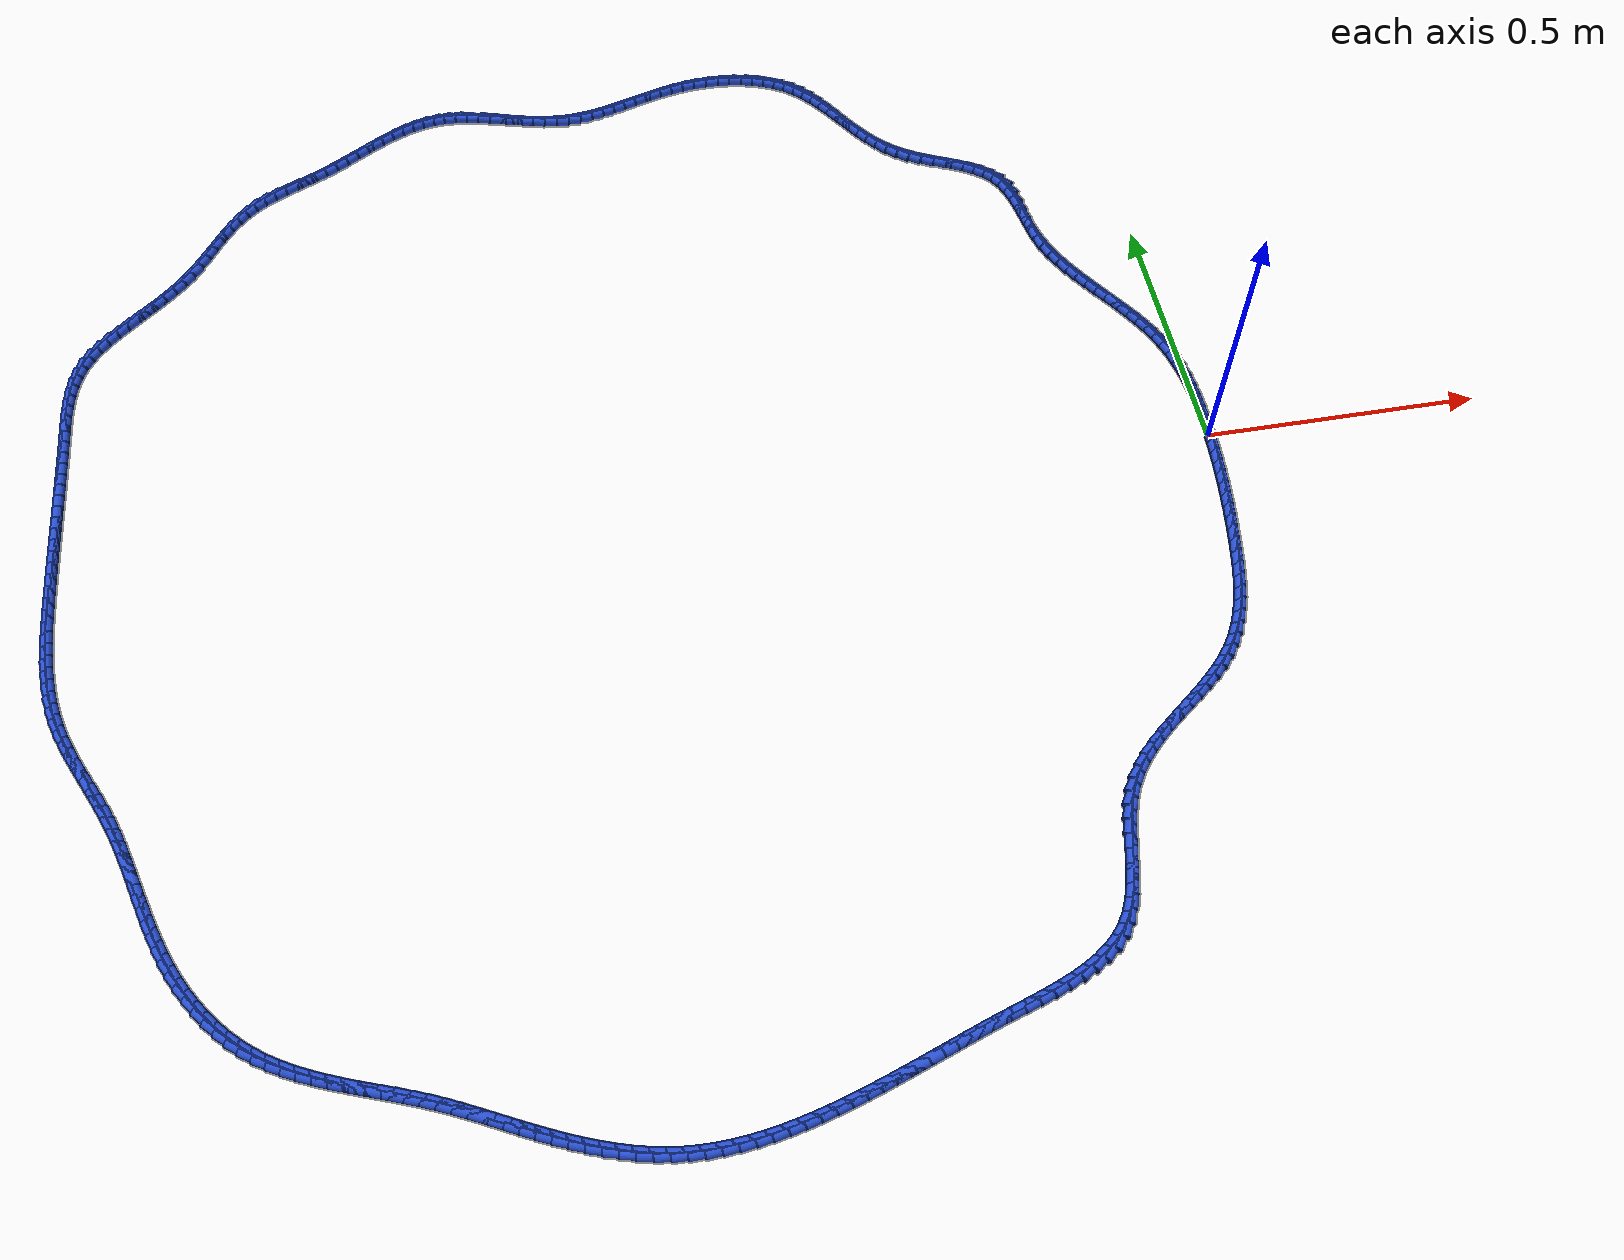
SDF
<sdf version="1.6">
 <world name="default">
  <light name="sun" type="directional">
   <pose>0 0 10 0 -0 0</pose>
   <diffuse>0.8 0.8 0.8 1</diffuse>
   <specular>0.2 0.2 0.2 1</specular>
   <attenuation>
    <range>1000</range>
    <constant>0.9</constant>
    <linear>0.01</linear>
    <quadratic>0.001</quadratic>
   </attenuation>
   <direction>-0.5 0.1 -0.9</direction>
  </light>
  <model name="ground_plane">
   <static>1</static>
   <link name="link">
    <collision name="collision">
     <geometry><plane><normal>0 0 1</normal><size>100 100</size></plane></geometry>
     <surface><friction><ode><mu>100</mu><mu2>50</mu2></ode></friction></surface>
    </collision>
    <visual name="visual">
     <cast_shadows>0</cast_shadows>
     <geometry><plane><normal>0 0 1</normal><size>100 100</size></plane></geometry>
     <material>
      <script><uri>file://media/materials/scripts/gazebo.material</uri><name>Gazebo/WhiteGlow</name></script>
     </material>
    </visual>
   </link>
  </model>
  <gravity>0 0 -9.8</gravity>
  <magnetic_field>6e-06 2.3e-05 -4.2e-05</magnetic_field>
  <atmosphere type="adiabatic"/>
  <physics name="default_physics" default="0" type="ode">
   <max_step_size>0.001</max_step_size>
   <real_time_factor>1</real_time_factor>
   <real_time_update_rate>1000</real_time_update_rate>
  </physics>
  <scene><ambient>0.4 0.4 0.4 1</ambient><background>0.7 0.7 0.7 1</background><shadows>1</shadows></scene>
  <spherical_coordinates>
   <surface_model>EARTH_WGS84</surface_model>
   <latitude_deg>0</latitude_deg>
   <longitude_deg>0</longitude_deg>
   <elevation>0</elevation>
   <heading_deg>0</heading_deg>
  </spherical_coordinates>
  <model name="line">
   <link name="link_0">
    <pose>4.336808689942018e-18 -2.0816681711721685e-17 0.01 0 1.57 1.5377371730256064</pose>
    <collision name="collision">
     <geometry><cylinder><radius>0.01</radius><length>0.08</length></cylinder></geometry>
    </collision>
    <visual name="visual">
     <material>
      <script><name>Gazebo/Blue</name><uri>file://media/materials/scripts/gazebo.material</uri></script>
     </material>
     <geometry><cylinder><radius>0.01</radius><length>0.08</length></cylinder></geometry>
    </visual>
   </link>
   <link name="link_1">
    <pose>0.0007970484209607412 0.024100980883869888 0.01 0 1.57 1.5590506642254127</pose>
    <collision name="collision">
     <geometry><cylinder><radius>0.01</radius><length>0.08</length></cylinder></geometry>
    </collision>
    <visual name="visual">
     <material>
      <script><name>Gazebo/Blue</name><uri>file://media/materials/scripts/gazebo.material</uri></script>
     </material>
     <geometry><cylinder><radius>0.01</radius><length>0.08</length></cylinder></geometry>
    </visual>
   </link>
   <link name="link_2">
    <pose>0.0010815445360322206 0.04832124348585979 0.01 0 1.57 -1.5562364600417415</pose>
    <collision name="collision">
     <geometry><cylinder><radius>0.01</radius><length>0.08</length></cylinder></geometry>
    </collision>
    <visual name="visual">
     <material>
      <script><name>Gazebo/Blue</name><uri>file://media/materials/scripts/gazebo.material</uri></script>
     </material>
     <geometry><cylinder><radius>0.01</radius><length>0.08</length></cylinder></geometry>
    </visual>
   </link>
   <link name="link_3">
    <pose>0.0007285085105565183 0.07256673174743694 0.01 0 1.57 -1.5246875000757079</pose>
    <collision name="collision">
     <geometry><cylinder><radius>0.01</radius><length>0.08</length></cylinder></geometry>
    </collision>
    <visual name="visual">
     <material>
      <script><name>Gazebo/Blue</name><uri>file://media/materials/scripts/gazebo.material</uri></script>
     </material>
     <geometry><cylinder><radius>0.01</radius><length>0.08</length></cylinder></geometry>
    </visual>
   </link>
   <link name="link_4">
    <pose>-0.00038703949012428886 0.0967433896100686 0.01 0 1.57 -1.4875768426590987</pose>
    <collision name="collision">
     <geometry><cylinder><radius>0.01</radius><length>0.08</length></cylinder></geometry>
    </collision>
    <visual name="visual">
     <material>
      <script><name>Gazebo/Blue</name><uri>file://media/materials/scripts/gazebo.material</uri></script>
     </material>
     <geometry><cylinder><radius>0.01</radius><length>0.08</length></cylinder></geometry>
    </visual>
   </link>
   <link name="link_5">
    <pose>-0.0023900793006681265 0.12075716101522205 0.01 0 1.57 -1.4445391100634075</pose>
    <collision name="collision">
     <geometry><cylinder><radius>0.01</radius><length>0.08</length></cylinder></geometry>
    </collision>
    <visual name="visual">
     <material>
      <script><name>Gazebo/Blue</name><uri>file://media/materials/scripts/gazebo.material</uri></script>
     </material>
     <geometry><cylinder><radius>0.01</radius><length>0.08</length></cylinder></geometry>
    </visual>
   </link>
   <link name="link_6">
    <pose>-0.005405590755732916 0.14451398990436462 0.01 0 1.57 -1.3951910916977617</pose>
    <collision name="collision">
     <geometry><cylinder><radius>0.01</radius><length>0.08</length></cylinder></geometry>
    </collision>
    <visual name="visual">
     <material>
      <script><name>Gazebo/Blue</name><uri>file://media/materials/scripts/gazebo.material</uri></script>
     </material>
     <geometry><cylinder><radius>0.01</radius><length>0.08</length></cylinder></geometry>
    </visual>
   </link>
   <link name="link_7">
    <pose>-0.009558553689976582 0.16791982021896348 0.01 0 1.57 -1.3391750716156336</pose>
    <collision name="collision">
     <geometry><cylinder><radius>0.01</radius><length>0.08</length></cylinder></geometry>
    </collision>
    <visual name="visual">
     <material>
      <script><name>Gazebo/Blue</name><uri>file://media/materials/scripts/gazebo.material</uri></script>
     </material>
     <geometry><cylinder><radius>0.01</radius><length>0.08</length></cylinder></geometry>
    </visual>
   </link>
   <link name="link_8">
    <pose>-0.014973947938057052 0.190880595900486 0.01 0 1.57 -1.276220242322087</pose>
    <collision name="collision">
     <geometry><cylinder><radius>0.01</radius><length>0.08</length></cylinder></geometry>
    </collision>
    <visual name="visual">
     <material>
      <script><name>Gazebo/Blue</name><uri>file://media/materials/scripts/gazebo.material</uri></script>
     </material>
     <geometry><cylinder><radius>0.01</radius><length>0.08</length></cylinder></geometry>
    </visual>
   </link>
   <link name="link_9">
    <pose>-0.02177675333463224 0.21330226089039936 0.01 0 1.57 -1.2068035065443747</pose>
    <collision name="collision">
     <geometry><cylinder><radius>0.01</radius><length>0.08</length></cylinder></geometry>
    </collision>
    <visual name="visual">
     <material>
      <script><name>Gazebo/Blue</name><uri>file://media/materials/scripts/gazebo.material</uri></script>
     </material>
     <geometry><cylinder><radius>0.01</radius><length>0.08</length></cylinder></geometry>
    </visual>
   </link>
   <link name="link_10">
    <pose>-0.030080076622343223 0.2350975762234323 0.01 0 1.57 -1.1405671205885406</pose>
    <collision name="collision">
     <geometry><cylinder><radius>0.01</radius><length>0.08</length></cylinder></geometry>
    </collision>
    <visual name="visual">
     <material>
      <script><name>Gazebo/Blue</name><uri>file://media/materials/scripts/gazebo.material</uri></script>
     </material>
     <geometry><cylinder><radius>0.01</radius><length>0.08</length></cylinder></geometry>
    </visual>
   </link>
   <link name="link_11">
    <pose>-0.039805034712374315 0.25628953644251956 0.01 0 1.57 -1.0856745129224168</pose>
    <collision name="collision">
     <geometry><cylinder><radius>0.01</radius><length>0.08</length></cylinder></geometry>
    </collision>
    <visual name="visual">
     <material>
      <script><name>Gazebo/Blue</name><uri>file://media/materials/scripts/gazebo.material</uri></script>
     </material>
     <geometry><cylinder><radius>0.01</radius><length>0.08</length></cylinder></geometry>
    </visual>
   </link>
   <link name="link_12">
    <pose>-0.050717258536227966 0.2769904104281333 0.01 0 1.57 -1.0425523027838146</pose>
    <collision name="collision">
     <geometry><cylinder><radius>0.01</radius><length>0.08</length></cylinder></geometry>
    </collision>
    <visual name="visual">
     <material>
      <script><name>Gazebo/Blue</name><uri>file://media/materials/scripts/gazebo.material</uri></script>
     </material>
     <geometry><cylinder><radius>0.01</radius><length>0.08</length></cylinder></geometry>
    </visual>
   </link>
   <link name="link_13">
    <pose>-0.06257790863728484 0.29731503379337926 0.01 0 1.57 -1.0110962908676804</pose>
    <collision name="collision">
     <geometry><cylinder><radius>0.01</radius><length>0.08</length></cylinder></geometry>
    </collision>
    <visual name="visual">
     <material>
      <script><name>Gazebo/Blue</name><uri>file://media/materials/scripts/gazebo.material</uri></script>
     </material>
     <geometry><cylinder><radius>0.01</radius><length>0.08</length></cylinder></geometry>
    </visual>
   </link>
   <link name="link_14">
    <pose>-0.07514814555892554 0.3173782421513631 0.01 0 1.57 -0.9910690757105136</pose>
    <collision name="collision">
     <geometry><cylinder><radius>0.01</radius><length>0.08</length></cylinder></geometry>
    </collision>
    <visual name="visual">
     <material>
      <script><name>Gazebo/Blue</name><uri>file://media/materials/scripts/gazebo.material</uri></script>
     </material>
     <geometry><cylinder><radius>0.01</radius><length>0.08</length></cylinder></geometry>
    </visual>
   </link>
   <link name="link_15">
    <pose>-0.08818912984453078 0.33729487111519063 0.01 0 1.57 -0.9822263687409355</pose>
    <collision name="collision">
     <geometry><cylinder><radius>0.01</radius><length>0.08</length></cylinder></geometry>
    </collision>
    <visual name="visual">
     <material>
      <script><name>Gazebo/Blue</name><uri>file://media/materials/scripts/gazebo.material</uri></script>
     </material>
     <geometry><cylinder><radius>0.01</radius><length>0.08</length></cylinder></geometry>
    </visual>
   </link>
   <link name="link_16">
    <pose>-0.1014620220374812 0.3571797562979676 0.01 0 1.57 -0.9843911157351981</pose>
    <collision name="collision">
     <geometry><cylinder><radius>0.01</radius><length>0.08</length></cylinder></geometry>
    </collision>
    <visual name="visual">
     <material>
      <script><name>Gazebo/Blue</name><uri>file://media/materials/scripts/gazebo.material</uri></script>
     </material>
     <geometry><cylinder><radius>0.01</radius><length>0.08</length></cylinder></geometry>
    </visual>
   </link>
   <link name="link_17">
    <pose>-0.11472798268115736 0.3771477333127995 0.01 0 1.57 -0.997482613853166</pose>
    <collision name="collision">
     <geometry><cylinder><radius>0.01</radius><length>0.08</length></cylinder></geometry>
    </collision>
    <visual name="visual">
     <material>
      <script><name>Gazebo/Blue</name><uri>file://media/materials/scripts/gazebo.material</uri></script>
     </material>
     <geometry><cylinder><radius>0.01</radius><length>0.08</length></cylinder></geometry>
    </visual>
   </link>
   <link name="link_18">
    <pose>-0.12774817231893995 0.3973136377727922 0.01 0 1.57 -1.0215063973636789</pose>
    <collision name="collision">
     <geometry><cylinder><radius>0.01</radius><length>0.08</length></cylinder></geometry>
    </collision>
    <visual name="visual">
     <material>
      <script><name>Gazebo/Blue</name><uri>file://media/materials/scripts/gazebo.material</uri></script>
     </material>
     <geometry><cylinder><radius>0.01</radius><length>0.08</length></cylinder></geometry>
    </visual>
   </link>
   <link name="link_19">
    <pose>-0.1402837514942097 0.41779230529105144 0.01 0 1.57 -1.056506563675862</pose>
    <collision name="collision">
     <geometry><cylinder><radius>0.01</radius><length>0.08</length></cylinder></geometry>
    </collision>
    <visual name="visual">
     <material>
      <script><name>Gazebo/Blue</name><uri>file://media/materials/scripts/gazebo.material</uri></script>
     </material>
     <geometry><cylinder><radius>0.01</radius><length>0.08</length></cylinder></geometry>
    </visual>
   </link>
   <link name="link_20">
    <pose>-0.15209588075034713 0.43869857148068286 0.01 0 1.57 -1.102479129949488</pose>
    <collision name="collision">
     <geometry><cylinder><radius>0.01</radius><length>0.08</length></cylinder></geometry>
    </collision>
    <visual name="visual">
     <material>
      <script><name>Gazebo/Blue</name><uri>file://media/materials/scripts/gazebo.material</uri></script>
     </material>
     <geometry><cylinder><radius>0.01</radius><length>0.08</length></cylinder></geometry>
    </visual>
   </link>
   <link name="link_21">
    <pose>-0.16294572063073295 0.4601472719547923 0.01 0 1.57 -1.1592462468740627</pose>
    <collision name="collision">
     <geometry><cylinder><radius>0.01</radius><length>0.08</length></cylinder></geometry>
    </collision>
    <visual name="visual">
     <material>
      <script><name>Gazebo/Blue</name><uri>file://media/materials/scripts/gazebo.material</uri></script>
     </material>
     <geometry><cylinder><radius>0.01</radius><length>0.08</length></cylinder></geometry>
    </visual>
   </link>
   <link name="link_22">
    <pose>-0.1725944316787478 0.48225324232648525 0.01 0 1.57 -1.2263000235672428</pose>
    <collision name="collision">
     <geometry><cylinder><radius>0.01</radius><length>0.08</length></cylinder></geometry>
    </collision>
    <visual name="visual">
     <material>
      <script><name>Gazebo/Blue</name><uri>file://media/materials/scripts/gazebo.material</uri></script>
     </material>
     <geometry><cylinder><radius>0.01</radius><length>0.08</length></cylinder></geometry>
    </visual>
   </link>
   <link name="link_23">
    <pose>-0.1808031744377723 0.5051313182088677 0.01 0 1.57 -1.3025626650573683</pose>
    <collision name="collision">
     <geometry><cylinder><radius>0.01</radius><length>0.08</length></cylinder></geometry>
    </collision>
    <visual name="visual">
     <material>
      <script><name>Gazebo/Blue</name><uri>file://media/materials/scripts/gazebo.material</uri></script>
     </material>
     <geometry><cylinder><radius>0.01</radius><length>0.08</length></cylinder></geometry>
    </visual>
   </link>
   <link name="link_24">
    <pose>-0.18733486048429673 0.5288952237328173 0.01 0 1.57 -1.3732433527757366</pose>
    <collision name="collision">
     <geometry><cylinder><radius>0.01</radius><length>0.08</length></cylinder></geometry>
    </collision>
    <visual name="visual">
     <material>
      <script><name>Gazebo/Blue</name><uri>file://media/materials/scripts/gazebo.material</uri></script>
     </material>
     <geometry><cylinder><radius>0.01</radius><length>0.08</length></cylinder></geometry>
    </visual>
   </link>
   <link name="link_25">
    <pose>-0.19225336715575275 0.5534676426127636 0.01 0 1.57 -1.4111423235205427</pose>
    <collision name="collision">
     <geometry><cylinder><radius>0.01</radius><length>0.08</length></cylinder></geometry>
    </collision>
    <visual name="visual">
     <material>
      <script><name>Gazebo/Blue</name><uri>file://media/materials/scripts/gazebo.material</uri></script>
     </material>
     <geometry><cylinder><radius>0.01</radius><length>0.08</length></cylinder></geometry>
    </visual>
   </link>
   <link name="link_26">
    <pose>-0.19626246417296553 0.5783650817707223 0.01 0 1.57 -1.414692538580771</pose>
    <collision name="collision">
     <geometry><cylinder><radius>0.01</radius><length>0.08</length></cylinder></geometry>
    </collision>
    <visual name="visual">
     <material>
      <script><name>Gazebo/Blue</name><uri>file://media/materials/scripts/gazebo.material</uri></script>
     </material>
     <geometry><cylinder><radius>0.01</radius><length>0.08</length></cylinder></geometry>
    </visual>
   </link>
   <link name="link_27">
    <pose>-0.20014780780355898 0.6030520699902222 0.01 0 1.57 -1.383097111100767</pose>
    <collision name="collision">
     <geometry><cylinder><radius>0.01</radius><length>0.08</length></cylinder></geometry>
    </collision>
    <visual name="visual">
     <material>
      <script><name>Gazebo/Blue</name><uri>file://media/materials/scripts/gazebo.material</uri></script>
     </material>
     <geometry><cylinder><radius>0.01</radius><length>0.08</length></cylinder></geometry>
    </visual>
   </link>
   <link name="link_28">
    <pose>-0.20469505431515722 0.6269931360547925 0.01 0 1.57 -1.3121633099585046</pose>
    <collision name="collision">
     <geometry><cylinder><radius>0.01</radius><length>0.08</length></cylinder></geometry>
    </collision>
    <visual name="visual">
     <material>
      <script><name>Gazebo/Blue</name><uri>file://media/materials/scripts/gazebo.material</uri></script>
     </material>
     <geometry><cylinder><radius>0.01</radius><length>0.08</length></cylinder></geometry>
    </visual>
   </link>
   <link name="link_29">
    <pose>-0.210689859975384 0.6496528087479614 0.01 0 1.57 -1.1948105988775166</pose>
    <collision name="collision">
     <geometry><cylinder><radius>0.01</radius><length>0.08</length></cylinder></geometry>
    </collision>
    <visual name="visual">
     <material>
      <script><name>Gazebo/Blue</name><uri>file://media/materials/scripts/gazebo.material</uri></script>
     </material>
     <geometry><cylinder><radius>0.01</radius><length>0.08</length></cylinder></geometry>
    </visual>
   </link>
   <link name="link_30">
    <pose>-0.21891788105186344 0.6704956168532586 0.01 0 1.57 -1.0243563953136636</pose>
    <collision name="collision">
     <geometry><cylinder><radius>0.01</radius><length>0.08</length></cylinder></geometry>
    </collision>
    <visual name="visual">
     <material>
      <script><name>Gazebo/Blue</name><uri>file://media/materials/scripts/gazebo.material</uri></script>
     </material>
     <geometry><cylinder><radius>0.01</radius><length>0.08</length></cylinder></geometry>
    </visual>
   </link>
   <link name="link_31">
    <pose>-0.23016432078421822 0.6889864337784675 0.01 0 1.57 -0.823109774391957</pose>
    <collision name="collision">
     <geometry><cylinder><radius>0.01</radius><length>0.08</length></cylinder></geometry>
    </collision>
    <visual name="visual">
     <material>
      <script><name>Gazebo/Blue</name><uri>file://media/materials/scripts/gazebo.material</uri></script>
     </material>
     <geometry><cylinder><radius>0.01</radius><length>0.08</length></cylinder></geometry>
    </visual>
   </link>
   <link name="link_32">
    <pose>-0.24487370348641282 0.7048492917926089 0.01 0 1.57 -0.658723296787749</pose>
    <collision name="collision">
     <geometry><cylinder><radius>0.01</radius><length>0.08</length></cylinder></geometry>
    </collision>
    <visual name="visual">
     <material>
      <script><name>Gazebo/Blue</name><uri>file://media/materials/scripts/gazebo.material</uri></script>
     </material>
     <geometry><cylinder><radius>0.01</radius><length>0.08</length></cylinder></geometry>
    </visual>
   </link>
   <link name="link_33">
    <pose>-0.26254471375626814 0.7185277356595703 0.01 0 1.57 -0.5433720480111619</pose>
    <collision name="collision">
     <geometry><cylinder><radius>0.01</radius><length>0.08</length></cylinder></geometry>
    </collision>
    <visual name="visual">
     <material>
      <script><name>Gazebo/Blue</name><uri>file://media/materials/scripts/gazebo.material</uri></script>
     </material>
     <geometry><cylinder><radius>0.01</radius><length>0.08</length></cylinder></geometry>
    </visual>
   </link>
   <link name="link_34">
    <pose>-0.2825132212821765 0.7305891655488476 0.01 0 1.57 -0.4714267252770129</pose>
    <collision name="collision">
     <geometry><cylinder><radius>0.01</radius><length>0.08</length></cylinder></geometry>
    </collision>
    <visual name="visual">
     <material>
      <script><name>Gazebo/Blue</name><uri>file://media/materials/scripts/gazebo.material</uri></script>
     </material>
     <geometry><cylinder><radius>0.01</radius><length>0.08</length></cylinder></geometry>
    </visual>
   </link>
   <link name="link_35">
    <pose>-0.3041150957525304 0.7416009816299373 0.01 0 1.57 -0.43649680693843845</pose>
    <collision name="collision">
     <geometry><cylinder><radius>0.01</radius><length>0.08</length></cylinder></geometry>
    </collision>
    <visual name="visual">
     <material>
      <script><name>Gazebo/Blue</name><uri>file://media/materials/scripts/gazebo.material</uri></script>
     </material>
     <geometry><cylinder><radius>0.01</radius><length>0.08</length></cylinder></geometry>
    </visual>
   </link>
   <link name="link_36">
    <pose>-0.3266862068557221 0.7521305840723356 0.01 0 1.57 -0.4344432025812066</pose>
    <collision name="collision">
     <geometry><cylinder><radius>0.01</radius><length>0.08</length></cylinder></geometry>
    </collision>
    <visual name="visual">
     <material>
      <script><name>Gazebo/Blue</name><uri>file://media/materials/scripts/gazebo.material</uri></script>
     </material>
     <geometry><cylinder><radius>0.01</radius><length>0.08</length></cylinder></geometry>
    </visual>
   </link>
   <link name="link_37">
    <pose>-0.3495624242801442 0.7627453730455389 0.01 0 1.57 -0.46395946269068633</pose>
    <collision name="collision">
     <geometry><cylinder><radius>0.01</radius><length>0.08</length></cylinder></geometry>
    </collision>
    <visual name="visual">
     <material>
      <script><name>Gazebo/Blue</name><uri>file://media/materials/scripts/gazebo.material</uri></script>
     </material>
     <geometry><cylinder><radius>0.01</radius><length>0.08</length></cylinder></geometry>
    </visual>
   </link>
   <link name="link_38">
    <pose>-0.372079617714189 0.7740127487190436 0.01 0 1.57 -0.5263082969305263</pose>
    <collision name="collision">
     <geometry><cylinder><radius>0.01</radius><length>0.08</length></cylinder></geometry>
    </collision>
    <visual name="visual">
     <material>
      <script><name>Gazebo/Blue</name><uri>file://media/materials/scripts/gazebo.material</uri></script>
     </material>
     <geometry><cylinder><radius>0.01</radius><length>0.08</length></cylinder></geometry>
    </visual>
   </link>
   <link name="link_39">
    <pose>-0.39357365684624906 0.7865001112623456 0.01 0 1.57 -0.6234887158550748</pose>
    <collision name="collision">
     <geometry><cylinder><radius>0.01</radius><length>0.08</length></cylinder></geometry>
    </collision>
    <visual name="visual">
     <material>
      <script><name>Gazebo/Blue</name><uri>file://media/materials/scripts/gazebo.material</uri></script>
     </material>
     <geometry><cylinder><radius>0.01</radius><length>0.08</length></cylinder></geometry>
    </visual>
   </link>
   <link name="link_40">
    <pose>-0.41339848496765896 0.8007579090677729 0.01 0 1.57 -0.732207605851496</pose>
    <collision name="collision">
     <geometry><cylinder><radius>0.01</radius><length>0.08</length></cylinder></geometry>
    </collision>
    <visual name="visual">
     <material>
      <script><name>Gazebo/Blue</name><uri>file://media/materials/scripts/gazebo.material</uri></script>
     </material>
     <geometry><cylinder><radius>0.01</radius><length>0.08</length></cylinder></geometry>
    </visual>
   </link>
   <link name="link_41">
    <pose>-0.4313649842175776 0.8169080138043303 0.01 0 1.57 -0.8238655063089911</pose>
    <collision name="collision">
     <geometry><cylinder><radius>0.01</radius><length>0.08</length></cylinder></geometry>
    </collision>
    <visual name="visual">
     <material>
      <script><name>Gazebo/Blue</name><uri>file://media/materials/scripts/gazebo.material</uri></script>
     </material>
     <geometry><cylinder><radius>0.01</radius><length>0.08</length></cylinder></geometry>
    </visual>
   </link>
   <link name="link_42">
    <pose>-0.4477651372034923 0.8346210585052847 0.01 0 1.57 -0.8957785052821226</pose>
    <collision name="collision">
     <geometry><cylinder><radius>0.01</radius><length>0.08</length></cylinder></geometry>
    </collision>
    <visual name="visual">
     <material>
      <script><name>Gazebo/Blue</name><uri>file://media/materials/scripts/gazebo.material</uri></script>
     </material>
     <geometry><cylinder><radius>0.01</radius><length>0.08</length></cylinder></geometry>
    </visual>
   </link>
   <link name="link_43">
    <pose>-0.4629138364821737 0.8535461882716753 0.01 0 1.57 -0.9479072521702695</pose>
    <collision name="collision">
     <geometry><cylinder><radius>0.01</radius><length>0.08</length></cylinder></geometry>
    </collision>
    <visual name="visual">
     <material>
      <script><name>Gazebo/Blue</name><uri>file://media/materials/scripts/gazebo.material</uri></script>
     </material>
     <geometry><cylinder><radius>0.01</radius><length>0.08</length></cylinder></geometry>
    </visual>
   </link>
   <link name="link_44">
    <pose>-0.47712597461039236 0.8733325482045406 0.01 0 1.57 -0.9807733343745144</pose>
    <collision name="collision">
     <geometry><cylinder><radius>0.01</radius><length>0.08</length></cylinder></geometry>
    </collision>
    <visual name="visual">
     <material>
      <script><name>Gazebo/Blue</name><uri>file://media/materials/scripts/gazebo.material</uri></script>
     </material>
     <geometry><cylinder><radius>0.01</radius><length>0.08</length></cylinder></geometry>
    </visual>
   </link>
   <link name="link_45">
    <pose>-0.4907164441449183 0.8936292834049192 0.01 0 1.57 -0.9948636064075415</pose>
    <collision name="collision">
     <geometry><cylinder><radius>0.01</radius><length>0.08</length></cylinder></geometry>
    </collision>
    <visual name="visual">
     <material>
      <script><name>Gazebo/Blue</name><uri>file://media/materials/scripts/gazebo.material</uri></script>
     </material>
     <geometry><cylinder><radius>0.01</radius><length>0.08</length></cylinder></geometry>
    </visual>
   </link>
   <link name="link_46">
    <pose>-0.504000137642522 0.9140855389738499 0.01 0 1.57 -0.9902829873642007</pose>
    <collision name="collision">
     <geometry><cylinder><radius>0.01</radius><length>0.08</length></cylinder></geometry>
    </collision>
    <visual name="visual">
     <material>
      <script><name>Gazebo/Blue</name><uri>file://media/materials/scripts/gazebo.material</uri></script>
     </material>
     <geometry><cylinder><radius>0.01</radius><length>0.08</length></cylinder></geometry>
    </visual>
   </link>
   <link name="link_47">
    <pose>-0.517291947659974 0.9343504600123713 0.01 0 1.57 -0.9666026711791768</pose>
    <collision name="collision">
     <geometry><cylinder><radius>0.01</radius><length>0.08</length></cylinder></geometry>
    </collision>
    <visual name="visual">
     <material>
      <script><name>Gazebo/Blue</name><uri>file://media/materials/scripts/gazebo.material</uri></script>
     </material>
     <geometry><cylinder><radius>0.01</radius><length>0.08</length></cylinder></geometry>
    </visual>
   </link>
   <link name="link_48">
    <pose>-0.5309067667540446 0.9540731916215222 0.01 0 1.57 -0.9228759148160085</pose>
    <collision name="collision">
     <geometry><cylinder><radius>0.01</radius><length>0.08</length></cylinder></geometry>
    </collision>
    <visual name="visual">
     <material>
      <script><name>Gazebo/Blue</name><uri>file://media/materials/scripts/gazebo.material</uri></script>
     </material>
     <geometry><cylinder><radius>0.01</radius><length>0.08</length></cylinder></geometry>
    </visual>
   </link>
   <link name="link_49">
    <pose>-0.5451594874815038 0.9729028789023408 0.01 0 1.57 -0.8578596229150195</pose>
    <collision name="collision">
     <geometry><cylinder><radius>0.01</radius><length>0.08</length></cylinder></geometry>
    </collision>
    <visual name="visual">
     <material>
      <script><name>Gazebo/Blue</name><uri>file://media/materials/scripts/gazebo.material</uri></script>
     </material>
     <geometry><cylinder><radius>0.01</radius><length>0.08</length></cylinder></geometry>
    </visual>
   </link>
   <link name="link_50">
    <pose>-0.5603650023991221 0.9904886669558661 0.01 0 1.57 -0.7705469808768325</pose>
    <collision name="collision">
     <geometry><cylinder><radius>0.01</radius><length>0.08</length></cylinder></geometry>
    </collision>
    <visual name="visual">
     <material>
      <script><name>Gazebo/Blue</name><uri>file://media/materials/scripts/gazebo.material</uri></script>
     </material>
     <geometry><cylinder><radius>0.01</radius><length>0.08</length></cylinder></geometry>
    </visual>
   </link>
   <link name="link_51">
    <pose>-0.57683820406367 1.0064797008831365 0.01 0 1.57 -0.6611400918502731</pose>
    <collision name="collision">
     <geometry><cylinder><radius>0.01</radius><length>0.08</length></cylinder></geometry>
    </collision>
    <visual name="visual">
     <material>
      <script><name>Gazebo/Blue</name><uri>file://media/materials/scripts/gazebo.material</uri></script>
     </material>
     <geometry><cylinder><radius>0.01</radius><length>0.08</length></cylinder></geometry>
    </visual>
   </link>
   <link name="link_52">
    <pose>-0.5948934781546033 1.0205255006504517 0.01 0 1.57 -0.5398579570727587</pose>
    <collision name="collision">
     <geometry><cylinder><radius>0.01</radius><length>0.08</length></cylinder></geometry>
    </collision>
    <visual name="visual">
     <material>
      <script><name>Gazebo/Blue</name><uri>file://media/materials/scripts/gazebo.material</uri></script>
     </material>
     <geometry><cylinder><radius>0.01</radius><length>0.08</length></cylinder></geometry>
    </visual>
   </link>
   <link name="link_53">
    <pose>-0.6146915484365888 1.0323892281490707 0.01 0 1.57 -0.4274421773303493</pose>
    <collision name="collision">
     <geometry><cylinder><radius>0.01</radius><length>0.08</length></cylinder></geometry>
    </collision>
    <visual name="visual">
     <material>
      <script><name>Gazebo/Blue</name><uri>file://media/materials/scripts/gazebo.material</uri></script>
     </material>
     <geometry><cylinder><radius>0.01</radius><length>0.08</length></cylinder></geometry>
    </visual>
   </link>
   <link name="link_54">
    <pose>-0.6360242259432919 1.0421068776955869 0.01 0 1.57 -0.32623134168544327</pose>
    <collision name="collision">
     <geometry><cylinder><radius>0.01</radius><length>0.08</length></cylinder></geometry>
    </collision>
    <visual name="visual">
     <material>
      <script><name>Gazebo/Blue</name><uri>file://media/materials/scripts/gazebo.material</uri></script>
     </material>
     <geometry><cylinder><radius>0.01</radius><length>0.08</length></cylinder></geometry>
    </visual>
   </link>
   <link name="link_55">
    <pose>-0.6586290972975799 1.049754545712776 0.01 0 1.57 -0.23499501403604114</pose>
    <collision name="collision">
     <geometry><cylinder><radius>0.01</radius><length>0.08</length></cylinder></geometry>
    </collision>
    <visual name="visual">
     <material>
      <script><name>Gazebo/Blue</name><uri>file://media/materials/scripts/gazebo.material</uri></script>
     </material>
     <geometry><cylinder><radius>0.01</radius><length>0.08</length></cylinder></geometry>
    </visual>
   </link>
   <link name="link_56">
    <pose>-0.682243749122319 1.0554083286234128 0.01 0 1.57 -0.15216776344641975</pose>
    <collision name="collision">
     <geometry><cylinder><radius>0.01</radius><length>0.08</length></cylinder></geometry>
    </collision>
    <visual name="visual">
     <material>
      <script><name>Gazebo/Blue</name><uri>file://media/materials/scripts/gazebo.material</uri></script>
     </material>
     <geometry><cylinder><radius>0.01</radius><length>0.08</length></cylinder></geometry>
    </visual>
   </link>
   <link name="link_57">
    <pose>-0.7066057680403758 1.0591443228502733 0.01 0 1.57 -0.07609154753678987</pose>
    <collision name="collision">
     <geometry><cylinder><radius>0.01</radius><length>0.08</length></cylinder></geometry>
    </collision>
    <visual name="visual">
     <material>
      <script><name>Gazebo/Blue</name><uri>file://media/materials/scripts/gazebo.material</uri></script>
     </material>
     <geometry><cylinder><radius>0.01</radius><length>0.08</length></cylinder></geometry>
    </visual>
   </link>
   <link name="link_58">
    <pose>-0.7314527406746172 1.061038624816132 0.01 0 1.57 -0.005133924898762644</pose>
    <collision name="collision">
     <geometry><cylinder><radius>0.01</radius><length>0.08</length></cylinder></geometry>
    </collision>
    <visual name="visual">
     <material>
      <script><name>Gazebo/Blue</name><uri>file://media/materials/scripts/gazebo.material</uri></script>
     </material>
     <geometry><cylinder><radius>0.01</radius><length>0.08</length></cylinder></geometry>
    </visual>
   </link>
   <link name="link_59">
    <pose>-0.7565222536479099 1.0611673309437646 0.01 0 1.57 0.062277162315601965</pose>
    <collision name="collision">
     <geometry><cylinder><radius>0.01</radius><length>0.08</length></cylinder></geometry>
    </collision>
    <visual name="visual">
     <material>
      <script><name>Gazebo/Blue</name><uri>file://media/materials/scripts/gazebo.material</uri></script>
     </material>
     <geometry><cylinder><radius>0.01</radius><length>0.08</length></cylinder></geometry>
    </visual>
   </link>
   <link name="link_60">
    <pose>-0.7815518935831205 1.0596065376559465 0.01 0 1.57 0.12764127700708167</pose>
    <collision name="collision">
     <geometry><cylinder><radius>0.01</radius><length>0.08</length></cylinder></geometry>
    </collision>
    <visual name="visual">
     <material>
      <script><name>Gazebo/Blue</name><uri>file://media/materials/scripts/gazebo.material</uri></script>
     </material>
     <geometry><cylinder><radius>0.01</radius><length>0.08</length></cylinder></geometry>
    </visual>
   </link>
   <link name="link_61">
    <pose>-0.806279998149785 1.0564329570912971 0.01 0 1.57 0.18837953735558405</pose>
    <collision name="collision">
     <geometry><cylinder><radius>0.01</radius><length>0.08</length></cylinder></geometry>
    </collision>
    <visual name="visual">
     <material>
      <script><name>Gazebo/Blue</name><uri>file://media/materials/scripts/gazebo.material</uri></script>
     </material>
     <geometry><cylinder><radius>0.01</radius><length>0.08</length></cylinder></geometry>
    </visual>
   </link>
   <link name="link_62">
    <pose>-0.830546700025307 1.051806753991003 0.01 0 1.57 0.2366429016731915</pose>
    <collision name="collision">
     <geometry><cylinder><radius>0.01</radius><length>0.08</length></cylinder></geometry>
    </collision>
    <visual name="visual">
     <material>
      <script><name>Gazebo/Blue</name><uri>file://media/materials/scripts/gazebo.material</uri></script>
     </material>
     <geometry><cylinder><radius>0.01</radius><length>0.08</length></cylinder></geometry>
    </visual>
   </link>
   <link name="link_63">
    <pose>-0.8543959957744661 1.046055222824195 0.01 0 1.57 0.271018231518018</pose>
    <collision name="collision">
     <geometry><cylinder><radius>0.01</radius><length>0.08</length></cylinder></geometry>
    </collision>
    <visual name="visual">
     <material>
      <script><name>Gazebo/Blue</name><uri>file://media/materials/scripts/gazebo.material</uri></script>
     </material>
     <geometry><cylinder><radius>0.01</radius><length>0.08</length></cylinder></geometry>
    </visual>
   </link>
   <link name="link_64">
    <pose>-0.8778961882794851 1.0395255846309814 0.01 0 1.57 0.29124762909165003</pose>
    <collision name="collision">
     <geometry><cylinder><radius>0.01</radius><length>0.08</length></cylinder></geometry>
    </collision>
    <visual name="visual">
     <material>
      <script><name>Gazebo/Blue</name><uri>file://media/materials/scripts/gazebo.material</uri></script>
     </material>
     <geometry><cylinder><radius>0.01</radius><length>0.08</length></cylinder></geometry>
    </visual>
   </link>
   <link name="link_65">
    <pose>-0.9011155804225881 1.0325650604514716 0.01 0 1.57 0.29711437225515364</pose>
    <collision name="collision">
     <geometry><cylinder><radius>0.01</radius><length>0.08</length></cylinder></geometry>
    </collision>
    <visual name="visual">
     <material>
      <script><name>Gazebo/Blue</name><uri>file://media/materials/scripts/gazebo.material</uri></script>
     </material>
     <geometry><cylinder><radius>0.01</radius><length>0.08</length></cylinder></geometry>
    </visual>
   </link>
   <link name="link_66">
    <pose>-0.9241224750859977 1.0255208713257742 0.01 0 1.57 0.2883167745336955</pose>
    <collision name="collision">
     <geometry><cylinder><radius>0.01</radius><length>0.08</length></cylinder></geometry>
    </collision>
    <visual name="visual">
     <material>
      <script><name>Gazebo/Blue</name><uri>file://media/materials/scripts/gazebo.material</uri></script>
     </material>
     <geometry><cylinder><radius>0.01</radius><length>0.08</length></cylinder></geometry>
    </visual>
   </link>
   <link name="link_67">
    <pose>-0.9469851751519373 1.0187402382939978 0.01 0 1.57 0.2644241346123407</pose>
    <collision name="collision">
     <geometry><cylinder><radius>0.01</radius><length>0.08</length></cylinder></geometry>
    </collision>
    <visual name="visual">
     <material>
      <script><name>Gazebo/Blue</name><uri>file://media/materials/scripts/gazebo.material</uri></script>
     </material>
     <geometry><cylinder><radius>0.01</radius><length>0.08</length></cylinder></geometry>
    </visual>
   </link>
   <link name="link_68">
    <pose>-0.9697719835026298 1.012570382396251 0.01 0 1.57 0.22492722466521078</pose>
    <collision name="collision">
     <geometry><cylinder><radius>0.01</radius><length>0.08</length></cylinder></geometry>
    </collision>
    <visual name="visual">
     <material>
      <script><name>Gazebo/Blue</name><uri>file://media/materials/scripts/gazebo.material</uri></script>
     </material>
     <geometry><cylinder><radius>0.01</radius><length>0.08</length></cylinder></geometry>
    </visual>
   </link>
   <link name="link_69">
    <pose>-0.9925512030202986 1.0073585246726433 0.01 0 1.57 0.1694048666344301</pose>
    <collision name="collision">
     <geometry><cylinder><radius>0.01</radius><length>0.08</length></cylinder></geometry>
    </collision>
    <visual name="visual">
     <material>
      <script><name>Gazebo/Blue</name><uri>file://media/materials/scripts/gazebo.material</uri></script>
     </material>
     <geometry><cylinder><radius>0.01</radius><length>0.08</length></cylinder></geometry>
    </visual>
   </link>
   <link name="link_70">
    <pose>-1.0153911365871675 1.0034518861632828 0.01 0 1.57 0.09782782879122977</pose>
    <collision name="collision">
     <geometry><cylinder><radius>0.01</radius><length>0.08</length></cylinder></geometry>
    </collision>
    <visual name="visual">
     <material>
      <script><name>Gazebo/Blue</name><uri>file://media/materials/scripts/gazebo.material</uri></script>
     </material>
     <geometry><cylinder><radius>0.01</radius><length>0.08</length></cylinder></geometry>
    </visual>
   </link>
   <link name="link_71">
    <pose>-1.0383600870854588 1.0011976879082787 0.01 0 1.57 0.010987519701659995</pose>
    <collision name="collision">
     <geometry><cylinder><radius>0.01</radius><length>0.08</length></cylinder></geometry>
    </collision>
    <visual name="visual">
     <material>
      <script><name>Gazebo/Blue</name><uri>file://media/materials/scripts/gazebo.material</uri></script>
     </material>
     <geometry><cylinder><radius>0.01</radius><length>0.08</length></cylinder></geometry>
    </visual>
   </link>
   <link name="link_72">
    <pose>-1.0615263552880936 1.0009431378363367 0.01 0 1.57 -0.08242207969816732</pose>
    <collision name="collision">
     <geometry><cylinder><radius>0.01</radius><length>0.08</length></cylinder></geometry>
    </collision>
    <visual name="visual">
     <material>
      <script><name>Gazebo/Blue</name><uri>file://media/materials/scripts/gazebo.material</uri></script>
     </material>
     <geometry><cylinder><radius>0.01</radius><length>0.08</length></cylinder></geometry>
    </visual>
   </link>
   <link name="link_73">
    <pose>-1.084932706964164 1.0028767185324472 0.01 0 1.57 -0.15783585836957162</pose>
    <collision name="collision">
     <geometry><cylinder><radius>0.01</radius><length>0.08</length></cylinder></geometry>
    </collision>
    <visual name="visual">
     <material>
      <script><name>Gazebo/Blue</name><uri>file://media/materials/scripts/gazebo.material</uri></script>
     </material>
     <geometry><cylinder><radius>0.01</radius><length>0.08</length></cylinder></geometry>
    </visual>
   </link>
   <link name="link_74">
    <pose>-1.1085327808702177 1.0066328999096443 0.01 0 1.57 -0.21141081417048613</pose>
    <collision name="collision">
     <geometry><cylinder><radius>0.01</radius><length>0.08</length></cylinder></geometry>
    </collision>
    <visual name="visual">
     <material>
      <script><name>Gazebo/Blue</name><uri>file://media/materials/scripts/gazebo.material</uri></script>
     </material>
     <geometry><cylinder><radius>0.01</radius><length>0.08</length></cylinder></geometry>
    </visual>
   </link>
   <link name="link_75">
    <pose>-1.1322607819037784 1.011725351195984 0.01 0 1.57 -0.2447751935968459</pose>
    <collision name="collision">
     <geometry><cylinder><radius>0.01</radius><length>0.08</length></cylinder></geometry>
    </collision>
    <visual name="visual">
     <material>
      <script><name>Gazebo/Blue</name><uri>file://media/materials/scripts/gazebo.material</uri></script>
     </material>
     <geometry><cylinder><radius>0.01</radius><length>0.08</length></cylinder></geometry>
    </visual>
   </link>
   <link name="link_76">
    <pose>-1.1560509149623694 1.0176677416195217 0.01 0 1.57 -0.2591472423313343</pose>
    <collision name="collision">
     <geometry><cylinder><radius>0.01</radius><length>0.08</length></cylinder></geometry>
    </collision>
    <visual name="visual">
     <material>
      <script><name>Gazebo/Blue</name><uri>file://media/materials/scripts/gazebo.material</uri></script>
     </material>
     <geometry><cylinder><radius>0.01</radius><length>0.08</length></cylinder></geometry>
    </visual>
   </link>
   <link name="link_77">
    <pose>-1.1798373849435146 1.023973740408313 0.01 0 1.57 -0.2550335485878208</pose>
    <collision name="collision">
     <geometry><cylinder><radius>0.01</radius><length>0.08</length></cylinder></geometry>
    </collision>
    <visual name="visual">
     <material>
      <script><name>Gazebo/Blue</name><uri>file://media/materials/scripts/gazebo.material</uri></script>
     </material>
     <geometry><cylinder><radius>0.01</radius><length>0.08</length></cylinder></geometry>
    </visual>
   </link>
   <link name="link_78">
    <pose>-1.2035543967447362 1.030157016790413 0.01 0 1.57 -0.2321180155048603</pose>
    <collision name="collision">
     <geometry><cylinder><radius>0.01</radius><length>0.08</length></cylinder></geometry>
    </collision>
    <visual name="visual">
     <material>
      <script><name>Gazebo/Blue</name><uri>file://media/materials/scripts/gazebo.material</uri></script>
     </material>
     <geometry><cylinder><radius>0.01</radius><length>0.08</length></cylinder></geometry>
    </visual>
   </link>
   <link name="link_79">
    <pose>-1.2271361552635571 1.0357312399938772 0.01 0 1.57 -0.189268415952359</pose>
    <collision name="collision">
     <geometry><cylinder><radius>0.01</radius><length>0.08</length></cylinder></geometry>
    </collision>
    <visual name="visual">
     <material>
      <script><name>Gazebo/Blue</name><uri>file://media/materials/scripts/gazebo.material</uri></script>
     </material>
     <geometry><cylinder><radius>0.01</radius><length>0.08</length></cylinder></geometry>
    </visual>
   </link>
   <link name="link_80">
    <pose>-1.2505168653975012 1.0402100792467615 0.01 0 1.57 -0.12469113344664708</pose>
    <collision name="collision">
     <geometry><cylinder><radius>0.01</radius><length>0.08</length></cylinder></geometry>
    </collision>
    <visual name="visual">
     <material>
      <script><name>Gazebo/Blue</name><uri>file://media/materials/scripts/gazebo.material</uri></script>
     </material>
     <geometry><cylinder><radius>0.01</radius><length>0.08</length></cylinder></geometry>
    </visual>
   </link>
   <link name="link_81">
    <pose>-1.2736307320440918 1.0431072037771207 0.01 0 1.57 -0.03637702489651573</pose>
    <collision name="collision">
     <geometry><cylinder><radius>0.01</radius><length>0.08</length></cylinder></geometry>
    </collision>
    <visual name="visual">
     <material>
      <script><name>Gazebo/Blue</name><uri>file://media/materials/scripts/gazebo.material</uri></script>
     </material>
     <geometry><cylinder><radius>0.01</radius><length>0.08</length></cylinder></geometry>
    </visual>
   </link>
   <link name="link_82">
    <pose>-1.2964119601008521 1.0439362828130108 0.01 0 1.57 0.07638808209749857</pose>
    <collision name="collision">
     <geometry><cylinder><radius>0.01</radius><length>0.08</length></cylinder></geometry>
    </collision>
    <visual name="visual">
     <material>
      <script><name>Gazebo/Blue</name><uri>file://media/materials/scripts/gazebo.material</uri></script>
     </material>
     <geometry><cylinder><radius>0.01</radius><length>0.08</length></cylinder></geometry>
    </visual>
   </link>
   <link name="link_83">
    <pose>-1.3187967264677185 1.042223019768948 0.01 0 1.57 0.19576556057275368</pose>
    <collision name="collision">
     <geometry><cylinder><radius>0.01</radius><length>0.08</length></cylinder></geometry>
    </collision>
    <visual name="visual">
     <material>
      <script><name>Gazebo/Blue</name><uri>file://media/materials/scripts/gazebo.material</uri></script>
     </material>
     <geometry><cylinder><radius>0.01</radius><length>0.08</length></cylinder></geometry>
    </visual>
   </link>
   <link name="link_84">
    <pose>-1.3407818603540727 1.0378632500613099 0.01 0 1.57 0.2992208809962638</pose>
    <collision name="collision">
     <geometry><cylinder><radius>0.01</radius><length>0.08</length></cylinder></geometry>
    </collision>
    <visual name="visual">
     <material>
      <script><name>Gazebo/Blue</name><uri>file://media/materials/scripts/gazebo.material</uri></script>
     </material>
     <geometry><cylinder><radius>0.01</radius><length>0.08</length></cylinder></geometry>
    </visual>
   </link>
   <link name="link_85">
    <pose>-1.362434798247867 1.0311836915180912 0.01 0 1.57 0.38418802656964063</pose>
    <collision name="collision">
     <geometry><cylinder><radius>0.01</radius><length>0.08</length></cylinder></geometry>
    </collision>
    <visual name="visual">
     <material>
      <script><name>Gazebo/Blue</name><uri>file://media/materials/scripts/gazebo.material</uri></script>
     </material>
     <geometry><cylinder><radius>0.01</radius><length>0.08</length></cylinder></geometry>
    </visual>
   </link>
   <link name="link_86">
    <pose>-1.3838269540597115 1.022535334273225 0.01 0 1.57 0.45091934533482214</pose>
    <collision name="collision">
     <geometry><cylinder><radius>0.01</radius><length>0.08</length></cylinder></geometry>
    </collision>
    <visual name="visual">
     <material>
      <script><name>Gazebo/Blue</name><uri>file://media/materials/scripts/gazebo.material</uri></script>
     </material>
     <geometry><cylinder><radius>0.01</radius><length>0.08</length></cylinder></geometry>
    </visual>
   </link>
   <link name="link_87">
    <pose>-1.4050297417002173 1.0122691684606446 0.01 0 1.57 0.5005217125748276</pose>
    <collision name="collision">
     <geometry><cylinder><radius>0.01</radius><length>0.08</length></cylinder></geometry>
    </collision>
    <visual name="visual">
     <material>
      <script><name>Gazebo/Blue</name><uri>file://media/materials/scripts/gazebo.material</uri></script>
     </material>
     <geometry><cylinder><radius>0.01</radius><length>0.08</length></cylinder></geometry>
    </visual>
   </link>
   <link name="link_88">
    <pose>-1.4261145750799933 1.000736184214284 0.01 0 1.57 0.5343102092895422</pose>
    <collision name="collision">
     <geometry><cylinder><radius>0.01</radius><length>0.08</length></cylinder></geometry>
    </collision>
    <visual name="visual">
     <material>
      <script><name>Gazebo/Blue</name><uri>file://media/materials/scripts/gazebo.material</uri></script>
     </material>
     <geometry><cylinder><radius>0.01</radius><length>0.08</length></cylinder></geometry>
    </visual>
   </link>
   <link name="link_89">
    <pose>-1.4471528681096508 0.9882873716680759 0.01 0 1.57 0.5534334207772104</pose>
    <collision name="collision">
     <geometry><cylinder><radius>0.01</radius><length>0.08</length></cylinder></geometry>
    </collision>
    <visual name="visual">
     <material>
      <script><name>Gazebo/Blue</name><uri>file://media/materials/scripts/gazebo.material</uri></script>
     </material>
     <geometry><cylinder><radius>0.01</radius><length>0.08</length></cylinder></geometry>
    </visual>
   </link>
   <link name="link_90">
    <pose>-1.4682160346998003 0.9752737209559543 0.01 0 1.57 0.5586958250278512</pose>
    <collision name="collision">
     <geometry><cylinder><radius>0.01</radius><length>0.08</length></cylinder></geometry>
    </collision>
    <visual name="visual">
     <material>
      <script><name>Gazebo/Blue</name><uri>file://media/materials/scripts/gazebo.material</uri></script>
     </material>
     <geometry><cylinder><radius>0.01</radius><length>0.08</length></cylinder></geometry>
    </visual>
   </link>
   <link name="link_91">
    <pose>-1.4893754887610522 0.9620462222118521 0.01 0 1.57 0.5504962522842153</pose>
    <collision name="collision">
     <geometry><cylinder><radius>0.01</radius><length>0.08</length></cylinder></geometry>
    </collision>
    <visual name="visual">
     <material>
      <script><name>Gazebo/Blue</name><uri>file://media/materials/scripts/gazebo.material</uri></script>
     </material>
     <geometry><cylinder><radius>0.01</radius><length>0.08</length></cylinder></geometry>
    </visual>
   </link>
   <link name="link_92">
    <pose>-1.5107026442040161 0.9489558655697033 0.01 0 1.57 0.5288317668239446</pose>
    <collision name="collision">
     <geometry><cylinder><radius>0.01</radius><length>0.08</length></cylinder></geometry>
    </collision>
    <visual name="visual">
     <material>
      <script><name>Gazebo/Blue</name><uri>file://media/materials/scripts/gazebo.material</uri></script>
     </material>
     <geometry><cylinder><radius>0.01</radius><length>0.08</length></cylinder></geometry>
    </visual>
   </link>
   <link name="link_93">
    <pose>-1.5322689149393034 0.9363536411634411 0.01 0 1.57 0.493755831559586</pose>
    <collision name="collision">
     <geometry><cylinder><radius>0.01</radius><length>0.08</length></cylinder></geometry>
    </collision>
    <visual name="visual">
     <material>
      <script><name>Gazebo/Blue</name><uri>file://media/materials/scripts/gazebo.material</uri></script>
     </material>
     <geometry><cylinder><radius>0.01</radius><length>0.08</length></cylinder></geometry>
    </visual>
   </link>
   <link name="link_94">
    <pose>-1.5541413616909237 0.9245814040939256 0.01 0 1.57 0.4598547742486325</pose>
    <collision name="collision">
     <geometry><cylinder><radius>0.01</radius><length>0.08</length></cylinder></geometry>
    </collision>
    <visual name="visual">
     <material>
      <script><name>Gazebo/Blue</name><uri>file://media/materials/scripts/gazebo.material</uri></script>
     </material>
     <geometry><cylinder><radius>0.01</radius><length>0.08</length></cylinder></geometry>
    </visual>
   </link>
   <link name="link_95">
    <pose>-1.5762262045556468 0.9136434901722317 0.01 0 1.57 0.44634239594070624</pose>
    <collision name="collision">
     <geometry><cylinder><radius>0.01</radius><length>0.08</length></cylinder></geometry>
    </collision>
    <visual name="visual">
     <material>
      <script><name>Gazebo/Blue</name><uri>file://media/materials/scripts/gazebo.material</uri></script>
     </material>
     <geometry><cylinder><radius>0.01</radius><length>0.08</length></cylinder></geometry>
    </visual>
   </link>
   <link name="link_96">
    <pose>-1.598225453869557 0.9031157070783618 0.01 0 1.57 0.4550290601198802</pose>
    <collision name="collision">
     <geometry><cylinder><radius>0.01</radius><length>0.08</length></cylinder></geometry>
    </collision>
    <visual name="visual">
     <material>
      <script><name>Gazebo/Blue</name><uri>file://media/materials/scripts/gazebo.material</uri></script>
     </material>
     <geometry><cylinder><radius>0.01</radius><length>0.08</length></cylinder></geometry>
    </visual>
   </link>
   <link name="link_97">
    <pose>-1.6198279376918658 0.8925461998749515 0.01 0 1.57 0.4869466151172061</pose>
    <collision name="collision">
     <geometry><cylinder><radius>0.01</radius><length>0.08</length></cylinder></geometry>
    </collision>
    <visual name="visual">
     <material>
      <script><name>Gazebo/Blue</name><uri>file://media/materials/scripts/gazebo.material</uri></script>
     </material>
     <geometry><cylinder><radius>0.01</radius><length>0.08</length></cylinder></geometry>
    </visual>
   </link>
   <link name="link_98">
    <pose>-1.6407224840817858 0.8814831136246382 0.01 0 1.57 0.5434939490834807</pose>
    <collision name="collision">
     <geometry><cylinder><radius>0.01</radius><length>0.08</length></cylinder></geometry>
    </collision>
    <visual name="visual">
     <material>
      <script><name>Gazebo/Blue</name><uri>file://media/materials/scripts/gazebo.material</uri></script>
     </material>
     <geometry><cylinder><radius>0.01</radius><length>0.08</length></cylinder></geometry>
    </visual>
   </link>
   <link name="link_99">
    <pose>-1.6605979210985276 0.8694745933900583 0.01 0 1.57 0.6259131954498796</pose>
    <collision name="collision">
     <geometry><cylinder><radius>0.01</radius><length>0.08</length></cylinder></geometry>
    </collision>
    <visual name="visual">
     <material>
      <script><name>Gazebo/Blue</name><uri>file://media/materials/scripts/gazebo.material</uri></script>
     </material>
     <geometry><cylinder><radius>0.01</radius><length>0.08</length></cylinder></geometry>
    </visual>
   </link>
   <link name="link_100">
    <pose>-1.6791430768013038 0.8560687842338481 0.01 0 1.57 0.7307482890715731</pose>
    <collision name="collision">
     <geometry><cylinder><radius>0.01</radius><length>0.08</length></cylinder></geometry>
    </collision>
    <visual name="visual">
     <material>
      <script><name>Gazebo/Blue</name><uri>file://media/materials/scripts/gazebo.material</uri></script>
     </material>
     <geometry><cylinder><radius>0.01</radius><length>0.08</length></cylinder></geometry>
    </visual>
   </link>
   <link name="link_101">
    <pose>-1.6960967388551773 0.8408737932004038 0.01 0 1.57 0.8279976988671648</pose>
    <collision name="collision">
     <geometry><cylinder><radius>0.01</radius><length>0.08</length></cylinder></geometry>
    </collision>
    <visual name="visual">
     <material>
      <script><name>Gazebo/Blue</name><uri>file://media/materials/scripts/gazebo.material</uri></script>
     </material>
     <geometry><cylinder><radius>0.01</radius><length>0.08</length></cylinder></geometry>
    </visual>
   </link>
   <link name="link_102">
    <pose>-1.7116041265971802 0.8239855303919092 0.01 0 1.57 0.9025857986357847</pose>
    <collision name="collision">
     <geometry><cylinder><radius>0.01</radius><length>0.08</length></cylinder></geometry>
    </collision>
    <visual name="visual">
     <material>
      <script><name>Gazebo/Blue</name><uri>file://media/materials/scripts/gazebo.material</uri></script>
     </material>
     <geometry><cylinder><radius>0.01</radius><length>0.08</length></cylinder></geometry>
    </visual>
   </link>
   <link name="link_103">
    <pose>-1.7260082708718312 0.8057373211143195 0.01 0 1.57 0.9547284005783051</pose>
    <collision name="collision">
     <geometry><cylinder><radius>0.01</radius><length>0.08</length></cylinder></geometry>
    </collision>
    <visual name="visual">
     <material>
      <script><name>Gazebo/Blue</name><uri>file://media/materials/scripts/gazebo.material</uri></script>
     </material>
     <geometry><cylinder><radius>0.01</radius><length>0.08</length></cylinder></geometry>
    </visual>
   </link>
   <link name="link_104">
    <pose>-1.7396535245655038 0.7864640774004691 0.01 0 1.57 0.9855103359040078</pose>
    <collision name="collision">
     <geometry><cylinder><radius>0.01</radius><length>0.08</length></cylinder></geometry>
    </collision>
    <visual name="visual">
     <material>
      <script><name>Gazebo/Blue</name><uri>file://media/materials/scripts/gazebo.material</uri></script>
     </material>
     <geometry><cylinder><radius>0.01</radius><length>0.08</length></cylinder></geometry>
    </visual>
   </link>
   <link name="link_105">
    <pose>-1.752884240564571 0.766500711283194 0.01 0 1.57 0.9960331178437193</pose>
    <collision name="collision">
     <geometry><cylinder><radius>0.01</radius><length>0.08</length></cylinder></geometry>
    </collision>
    <visual name="visual">
     <material>
      <script><name>Gazebo/Blue</name><uri>file://media/materials/scripts/gazebo.material</uri></script>
     </material>
     <geometry><cylinder><radius>0.01</radius><length>0.08</length></cylinder></geometry>
    </visual>
   </link>
   <link name="link_106">
    <pose>-1.7660447717554064 0.7461821347953289 0.01 0 1.57 0.9870452478945319</pose>
    <collision name="collision">
     <geometry><cylinder><radius>0.01</radius><length>0.08</length></cylinder></geometry>
    </collision>
    <visual name="visual">
     <material>
      <script><name>Gazebo/Blue</name><uri>file://media/materials/scripts/gazebo.material</uri></script>
     </material>
     <geometry><cylinder><radius>0.01</radius><length>0.08</length></cylinder></geometry>
    </visual>
   </link>
   <link name="link_107">
    <pose>-1.7794794710243846 0.7258432599697092 0.01 0 1.57 0.9588568464816027</pose>
    <collision name="collision">
     <geometry><cylinder><radius>0.01</radius><length>0.08</length></cylinder></geometry>
    </collision>
    <visual name="visual">
     <material>
      <script><name>Gazebo/Blue</name><uri>file://media/materials/scripts/gazebo.material</uri></script>
     </material>
     <geometry><cylinder><radius>0.01</radius><length>0.08</length></cylinder></geometry>
    </visual>
   </link>
   <link name="link_108">
    <pose>-1.793532691257877 0.7058189988391694 0.01 0 1.57 0.9114645203342018</pose>
    <collision name="collision">
     <geometry><cylinder><radius>0.01</radius><length>0.08</length></cylinder></geometry>
    </collision>
    <visual name="visual">
     <material>
      <script><name>Gazebo/Blue</name><uri>file://media/materials/scripts/gazebo.material</uri></script>
     </material>
     <geometry><cylinder><radius>0.01</radius><length>0.08</length></cylinder></geometry>
    </visual>
   </link>
   <link name="link_109">
    <pose>-1.8085487853422597 0.6864442634365454 0.01 0 1.57 0.8468102616640416</pose>
    <collision name="collision">
     <geometry><cylinder><radius>0.01</radius><length>0.08</length></cylinder></geometry>
    </collision>
    <visual name="visual">
     <material>
      <script><name>Gazebo/Blue</name><uri>file://media/materials/scripts/gazebo.material</uri></script>
     </material>
     <geometry><cylinder><radius>0.01</radius><length>0.08</length></cylinder></geometry>
    </visual>
   </link>
   <link name="link_110">
    <pose>-1.8248346660096881 0.6680243432362047 0.01 0 1.57 0.786531295431837</pose>
    <collision name="collision">
     <geometry><cylinder><radius>0.01</radius><length>0.08</length></cylinder></geometry>
    </collision>
    <visual name="visual">
     <material>
      <script><name>Gazebo/Blue</name><uri>file://media/materials/scripts/gazebo.material</uri></script>
     </material>
     <geometry><cylinder><radius>0.01</radius><length>0.08</length></cylinder></geometry>
    </visual>
   </link>
   <link name="link_111">
    <pose>-1.8422828018042046 0.6505366204842774 0.01 0 1.57 0.7436578281432166</pose>
    <collision name="collision">
     <geometry><cylinder><radius>0.01</radius><length>0.08</length></cylinder></geometry>
    </collision>
    <visual name="visual">
     <material>
      <script><name>Gazebo/Blue</name><uri>file://media/materials/scripts/gazebo.material</uri></script>
     </material>
     <geometry><cylinder><radius>0.01</radius><length>0.08</length></cylinder></geometry>
    </visual>
   </link>
   <link name="link_112">
    <pose>-1.8605278331931914 0.6337544844830793 0.01 0 1.57 0.7178476520900512</pose>
    <collision name="collision">
     <geometry><cylinder><radius>0.01</radius><length>0.08</length></cylinder></geometry>
    </collision>
    <visual name="visual">
     <material>
      <script><name>Gazebo/Blue</name><uri>file://media/materials/scripts/gazebo.material</uri></script>
     </material>
     <geometry><cylinder><radius>0.01</radius><length>0.08</length></cylinder></geometry>
    </visual>
   </link>
   <link name="link_113">
    <pose>-1.879200513104859 0.6174482487234398 0.01 0 1.57 0.7087742691177175</pose>
    <collision name="collision">
     <geometry><cylinder><radius>0.01</radius><length>0.08</length></cylinder></geometry>
    </collision>
    <visual name="visual">
     <material>
      <script><name>Gazebo/Blue</name><uri>file://media/materials/scripts/gazebo.material</uri></script>
     </material>
     <geometry><cylinder><radius>0.01</radius><length>0.08</length></cylinder></geometry>
    </visual>
   </link>
   <link name="link_114">
    <pose>-1.8979315944674169 0.6013882266961902 0.01 0 1.57 0.7165436397375144</pose>
    <collision name="collision">
     <geometry><cylinder><radius>0.01</radius><length>0.08</length></cylinder></geometry>
    </collision>
    <visual name="visual">
     <material>
      <script><name>Gazebo/Blue</name><uri>file://media/materials/scripts/gazebo.material</uri></script>
     </material>
     <geometry><cylinder><radius>0.01</radius><length>0.08</length></cylinder></geometry>
    </visual>
   </link>
   <link name="link_115">
    <pose>-1.916351830209078 0.5853447318921601 0.01 0 1.57 0.7417896890310126</pose>
    <collision name="collision">
     <geometry><cylinder><radius>0.01</radius><length>0.08</length></cylinder></geometry>
    </collision>
    <visual name="visual">
     <material>
      <script><name>Gazebo/Blue</name><uri>file://media/materials/scripts/gazebo.material</uri></script>
     </material>
     <geometry><cylinder><radius>0.01</radius><length>0.08</length></cylinder></geometry>
    </visual>
   </link>
   <link name="link_116">
    <pose>-1.9340919732580513 0.5690880778021798 0.01 0 1.57 0.7856586162709317</pose>
    <collision name="collision">
     <geometry><cylinder><radius>0.01</radius><length>0.08</length></cylinder></geometry>
    </collision>
    <visual name="visual">
     <material>
      <script><name>Gazebo/Blue</name><uri>file://media/materials/scripts/gazebo.material</uri></script>
     </material>
     <geometry><cylinder><radius>0.01</radius><length>0.08</length></cylinder></geometry>
    </visual>
   </link>
   <link name="link_117">
    <pose>-1.9507827765425483 0.5523885779170792 0.01 0 1.57 0.8496338841705936</pose>
    <collision name="collision">
     <geometry><cylinder><radius>0.01</radius><length>0.08</length></cylinder></geometry>
    </collision>
    <visual name="visual">
     <material>
      <script><name>Gazebo/Blue</name><uri>file://media/materials/scripts/gazebo.material</uri></script>
     </material>
     <geometry><cylinder><radius>0.01</radius><length>0.08</length></cylinder></geometry>
    </visual>
   </link>
   <link name="link_118">
    <pose>-1.96605499299078 0.5350165457276892 0.01 0 1.57 0.9350909355980366</pose>
    <collision name="collision">
     <geometry><cylinder><radius>0.01</radius><length>0.08</length></cylinder></geometry>
    </collision>
    <visual name="visual">
     <material>
      <script><name>Gazebo/Blue</name><uri>file://media/materials/scripts/gazebo.material</uri></script>
     </material>
     <geometry><cylinder><radius>0.01</radius><length>0.08</length></cylinder></geometry>
    </visual>
   </link>
   <link name="link_119">
    <pose>-1.9795393755309576 0.5167422947248396 0.01 0 1.57 1.0424511098738443</pose>
    <collision name="collision">
     <geometry><cylinder><radius>0.01</radius><length>0.08</length></cylinder></geometry>
    </collision>
    <visual name="visual">
     <material>
      <script><name>Gazebo/Blue</name><uri>file://media/materials/scripts/gazebo.material</uri></script>
     </material>
     <geometry><cylinder><radius>0.01</radius><length>0.08</length></cylinder></geometry>
    </visual>
   </link>
   <link name="link_120">
    <pose>-1.9908666770912906 0.4973361383993608 0.01 0 1.57 1.1684162316057913</pose>
    <collision name="collision">
     <geometry><cylinder><radius>0.01</radius><length>0.08</length></cylinder></geometry>
    </collision>
    <visual name="visual">
     <material>
      <script><name>Gazebo/Blue</name><uri>file://media/materials/scripts/gazebo.material</uri></script>
     </material>
     <geometry><cylinder><radius>0.01</radius><length>0.08</length></cylinder></geometry>
    </visual>
   </link>
   <link name="link_121">
    <pose>-1.999697527051597 0.476587038721617 0.01 0 1.57 1.2874068565234789</pose>
    <collision name="collision">
     <geometry><cylinder><radius>0.01</radius><length>0.08</length></cylinder></geometry>
    </collision>
    <visual name="visual">
     <material>
      <script><name>Gazebo/Blue</name><uri>file://media/materials/scripts/gazebo.material</uri></script>
     </material>
     <geometry><cylinder><radius>0.01</radius><length>0.08</length></cylinder></geometry>
    </visual>
   </link>
   <link name="link_122">
    <pose>-2.006115853661543 0.45454817512712775 0.01 0 1.57 1.3822493249259864</pose>
    <collision name="collision">
     <geometry><cylinder><radius>0.01</radius><length>0.08</length></cylinder></geometry>
    </collision>
    <visual name="visual">
     <material>
      <script><name>Gazebo/Blue</name><uri>file://media/materials/scripts/gazebo.material</uri></script>
     </material>
     <geometry><cylinder><radius>0.01</radius><length>0.08</length></cylinder></geometry>
    </visual>
   </link>
   <link name="link_123">
    <pose>-2.010519710441817 0.4314687998235448 0.01 0 1.57 1.4542204618017907</pose>
    <collision name="collision">
     <geometry><cylinder><radius>0.01</radius><length>0.08</length></cylinder></geometry>
    </collision>
    <visual name="visual">
     <material>
      <script><name>Gazebo/Blue</name><uri>file://media/materials/scripts/gazebo.material</uri></script>
     </material>
     <geometry><cylinder><radius>0.01</radius><length>0.08</length></cylinder></geometry>
    </visual>
   </link>
   <link name="link_124">
    <pose>-2.013314581821153 0.4076028032914421 0.01 0 1.57 1.5056650798893778</pose>
    <collision name="collision">
     <geometry><cylinder><radius>0.01</radius><length>0.08</length></cylinder></geometry>
    </collision>
    <visual name="visual">
     <material>
      <script><name>Gazebo/Blue</name><uri>file://media/materials/scripts/gazebo.material</uri></script>
     </material>
     <geometry><cylinder><radius>0.01</radius><length>0.08</length></cylinder></geometry>
    </visual>
   </link>
   <link name="link_125">
    <pose>-2.0149059522282804 0.3832040760113937 0.01 0 1.57 1.5386586086296468</pose>
    <collision name="collision">
     <geometry><cylinder><radius>0.01</radius><length>0.08</length></cylinder></geometry>
    </collision>
    <visual name="visual">
     <material>
      <script><name>Gazebo/Blue</name><uri>file://media/materials/scripts/gazebo.material</uri></script>
     </material>
     <geometry><cylinder><radius>0.01</radius><length>0.08</length></cylinder></geometry>
    </visual>
   </link>
   <link name="link_126">
    <pose>-2.01569930609193 0.35852650846397327 0.01 0 1.57 1.5545718030859106</pose>
    <collision name="collision">
     <geometry><cylinder><radius>0.01</radius><length>0.08</length></cylinder></geometry>
    </collision>
    <visual name="visual">
     <material>
      <script><name>Gazebo/Blue</name><uri>file://media/materials/scripts/gazebo.material</uri></script>
     </material>
     <geometry><cylinder><radius>0.01</radius><length>0.08</length></cylinder></geometry>
    </visual>
   </link>
   <link name="link_127">
    <pose>-2.016100127840835 0.33382399112975586 0.01 0 1.57 1.5557562844316384</pose>
    <collision name="collision">
     <geometry><cylinder><radius>0.01</radius><length>0.08</length></cylinder></geometry>
    </collision>
    <visual name="visual">
     <material>
      <script><name>Gazebo/Blue</name><uri>file://media/materials/scripts/gazebo.material</uri></script>
     </material>
     <geometry><cylinder><radius>0.01</radius><length>0.08</length></cylinder></geometry>
    </visual>
   </link>
   <link name="link_128">
    <pose>-2.0164687058212523 0.3093193933391533 0.01 0 1.57 1.5532172200344816</pose>
    <collision name="collision">
     <geometry><cylinder><radius>0.01</radius><length>0.08</length></cylinder></geometry>
    </collision>
    <visual name="visual">
     <material>
      <script><name>Gazebo/Blue</name><uri>file://media/materials/scripts/gazebo.material</uri></script>
     </material>
     <geometry><cylinder><radius>0.01</radius><length>0.08</length></cylinder></geometry>
    </visual>
   </link>
   <link name="link_129">
    <pose>-2.016895378762641 0.28505029961157613 0.01 0 1.57 1.5510474250908324</pose>
    <collision name="collision">
     <geometry><cylinder><radius>0.01</radius><length>0.08</length></cylinder></geometry>
    </collision>
    <visual name="visual">
     <material>
      <script><name>Gazebo/Blue</name><uri>file://media/materials/scripts/gazebo.material</uri></script>
     </material>
     <geometry><cylinder><radius>0.01</radius><length>0.08</length></cylinder></geometry>
    </visual>
   </link>
   <link name="link_130">
    <pose>-2.0173706880589206 0.26098579675685135 0.01 0 1.57 1.5492715364120768</pose>
    <collision name="collision">
     <geometry><cylinder><radius>0.01</radius><length>0.08</length></cylinder></geometry>
    </collision>
    <visual name="visual">
     <material>
      <script><name>Gazebo/Blue</name><uri>file://media/materials/scripts/gazebo.material</uri></script>
     </material>
     <geometry><cylinder><radius>0.01</radius><length>0.08</length></cylinder></geometry>
    </visual>
   </link>
   <link name="link_131">
    <pose>-2.0178850148646887 0.2370948616016437 0.01 0 1.57 1.5479050706010848</pose>
    <collision name="collision">
     <geometry><cylinder><radius>0.01</radius><length>0.08</length></cylinder></geometry>
    </collision>
    <visual name="visual">
     <material>
      <script><name>Gazebo/Blue</name><uri>file://media/materials/scripts/gazebo.material</uri></script>
     </material>
     <geometry><cylinder><radius>0.01</radius><length>0.08</length></cylinder></geometry>
    </visual>
   </link>
   <link name="link_132">
    <pose>-2.0184287403345436 0.21334647097261883 0.01 0 1.57 1.5469607434012527</pose>
    <collision name="collision">
     <geometry><cylinder><radius>0.01</radius><length>0.08</length></cylinder></geometry>
    </collision>
    <visual name="visual">
     <material>
      <script><name>Gazebo/Blue</name><uri>file://media/materials/scripts/gazebo.material</uri></script>
     </material>
     <geometry><cylinder><radius>0.01</radius><length>0.08</length></cylinder></geometry>
    </visual>
   </link>
   <link name="link_133">
    <pose>-2.0189922456230818 0.18970960169644127 0.01 0 1.57 1.5464482261135721</pose>
    <collision name="collision">
     <geometry><cylinder><radius>0.01</radius><length>0.08</length></cylinder></geometry>
    </collision>
    <visual name="visual">
     <material>
      <script><name>Gazebo/Blue</name><uri>file://media/materials/scripts/gazebo.material</uri></script>
     </material>
     <geometry><cylinder><radius>0.01</radius><length>0.08</length></cylinder></geometry>
    </visual>
   </link>
   <link name="link_134">
    <pose>-2.019565911884902 0.16615323059977608 0.01 0 1.57 1.5463739521736168</pose>
    <collision name="collision">
     <geometry><cylinder><radius>0.01</radius><length>0.08</length></cylinder></geometry>
    </collision>
    <visual name="visual">
     <material>
      <script><name>Gazebo/Blue</name><uri>file://media/materials/scripts/gazebo.material</uri></script>
     </material>
     <geometry><cylinder><radius>0.01</radius><length>0.08</length></cylinder></geometry>
    </visual>
   </link>
   <link name="link_135">
    <pose>-2.020140120274601 0.1426463345092877 0.01 0 1.57 1.5467409804523546</pose>
    <collision name="collision">
     <geometry><cylinder><radius>0.01</radius><length>0.08</length></cylinder></geometry>
    </collision>
    <visual name="visual">
     <material>
      <script><name>Gazebo/Blue</name><uri>file://media/materials/scripts/gazebo.material</uri></script>
     </material>
     <geometry><cylinder><radius>0.01</radius><length>0.08</length></cylinder></geometry>
    </visual>
   </link>
   <link name="link_136">
    <pose>-2.020705251946777 0.11915789025164192 0.01 0 1.57 1.54754892012731</pose>
    <collision name="collision">
     <geometry><cylinder><radius>0.01</radius><length>0.08</length></cylinder></geometry>
    </collision>
    <visual name="visual">
     <material>
      <script><name>Gazebo/Blue</name><uri>file://media/materials/scripts/gazebo.material</uri></script>
     </material>
     <geometry><cylinder><radius>0.01</radius><length>0.08</length></cylinder></geometry>
    </visual>
   </link>
   <link name="link_137">
    <pose>-2.021251688056028 0.0956568746535033 0.01 0 1.57 1.5487939199948062</pose>
    <collision name="collision">
     <geometry><cylinder><radius>0.01</radius><length>0.08</length></cylinder></geometry>
    </collision>
    <visual name="visual">
     <material>
      <script><name>Gazebo/Blue</name><uri>file://media/materials/scripts/gazebo.material</uri></script>
     </material>
     <geometry><cylinder><radius>0.01</radius><length>0.08</length></cylinder></geometry>
    </visual>
   </link>
   <link name="link_138">
    <pose>-2.021769809756951 0.07211226454153677 0.01 0 1.57 1.5504687229603618</pose>
    <collision name="collision">
     <geometry><cylinder><radius>0.01</radius><length>0.08</length></cylinder></geometry>
    </collision>
    <visual name="visual">
     <material>
      <script><name>Gazebo/Blue</name><uri>file://media/materials/scripts/gazebo.material</uri></script>
     </material>
     <geometry><cylinder><radius>0.01</radius><length>0.08</length></cylinder></geometry>
    </visual>
   </link>
   <link name="link_139">
    <pose>-2.022249998204144 0.04849303674240731 0.01 0 1.57 1.552562784255849</pose>
    <collision name="collision">
     <geometry><cylinder><radius>0.01</radius><length>0.08</length></cylinder></geometry>
    </collision>
    <visual name="visual">
     <material>
      <script><name>Gazebo/Blue</name><uri>file://media/materials/scripts/gazebo.material</uri></script>
     </material>
     <geometry><cylinder><radius>0.01</radius><length>0.08</length></cylinder></geometry>
    </visual>
   </link>
   <link name="link_140">
    <pose>-2.0226826345522047 0.024768168082779485 0.01 0 1.57 1.5550985247395983</pose>
    <collision name="collision">
     <geometry><cylinder><radius>0.01</radius><length>0.08</length></cylinder></geometry>
    </collision>
    <visual name="visual">
     <material>
      <script><name>Gazebo/Blue</name><uri>file://media/materials/scripts/gazebo.material</uri></script>
     </material>
     <geometry><cylinder><radius>0.01</radius><length>0.08</length></cylinder></geometry>
    </visual>
   </link>
   <link name="link_141">
    <pose>-2.023057227948224 0.0009073355299629441 0.01 0 1.57 1.5597617232590624</pose>
    <collision name="collision">
     <geometry><cylinder><radius>0.01</radius><length>0.08</length></cylinder></geometry>
    </collision>
    <visual name="visual">
     <material>
      <script><name>Gazebo/Blue</name><uri>file://media/materials/scripts/gazebo.material</uri></script>
     </material>
     <geometry><cylinder><radius>0.01</radius><length>0.08</length></cylinder></geometry>
    </visual>
   </link>
   <link name="link_142">
    <pose>-2.0233220026584045 -0.023086636042471863 0.01 0 1.57 1.5689341374883188</pose>
    <collision name="collision">
     <geometry><cylinder><radius>0.01</radius><length>0.08</length></cylinder></geometry>
    </collision>
    <visual name="visual">
     <material>
      <script><name>Gazebo/Blue</name><uri>file://media/materials/scripts/gazebo.material</uri></script>
     </material>
     <geometry><cylinder><radius>0.01</radius><length>0.08</length></cylinder></geometry>
    </visual>
   </link>
   <link name="link_143">
    <pose>-2.023366839464035 -0.04716407738772726 0.01 0 1.57 -1.5587827973784363</pose>
    <collision name="collision">
     <geometry><cylinder><radius>0.01</radius><length>0.08</length></cylinder></geometry>
    </collision>
    <visual name="visual">
     <material>
      <script><name>Gazebo/Blue</name><uri>file://media/materials/scripts/gazebo.material</uri></script>
     </material>
     <geometry><cylinder><radius>0.01</radius><length>0.08</length></cylinder></geometry>
    </visual>
   </link>
   <link name="link_144">
    <pose>-2.023077206975355 -0.07127177669743998 0.01 0 1.57 -1.540137844850305</pose>
    <collision name="collision">
     <geometry><cylinder><radius>0.01</radius><length>0.08</length></cylinder></geometry>
    </collision>
    <visual name="visual">
     <material>
      <script><name>Gazebo/Blue</name><uri>file://media/materials/scripts/gazebo.material</uri></script>
     </material>
     <geometry><cylinder><radius>0.01</radius><length>0.08</length></cylinder></geometry>
    </visual>
   </link>
   <link name="link_145">
    <pose>-2.0223385738026076 -0.09535652216324693 0.01 0 1.57 -1.5166119209188074</pose>
    <collision name="collision">
     <geometry><cylinder><radius>0.01</radius><length>0.08</length></cylinder></geometry>
    </collision>
    <visual name="visual">
     <material>
      <script><name>Gazebo/Blue</name><uri>file://media/materials/scripts/gazebo.material</uri></script>
     </material>
     <geometry><cylinder><radius>0.01</radius><length>0.08</length></cylinder></geometry>
    </visual>
   </link>
   <link name="link_146">
    <pose>-2.021036408556032 -0.11936510197678567 0.01 0 1.57 -1.4880587186526688</pose>
    <collision name="collision">
     <geometry><cylinder><radius>0.01</radius><length>0.08</length></cylinder></geometry>
    </collision>
    <visual name="visual">
     <material>
      <script><name>Gazebo/Blue</name><uri>file://media/materials/scripts/gazebo.material</uri></script>
     </material>
     <geometry><cylinder><radius>0.01</radius><length>0.08</length></cylinder></geometry>
    </visual>
   </link>
   <link name="link_147">
    <pose>-2.0190561798458715 -0.14324430432969154 0.01 0 1.57 -1.4543125406291841</pose>
    <collision name="collision">
     <geometry><cylinder><radius>0.01</radius><length>0.08</length></cylinder></geometry>
    </collision>
    <visual name="visual">
     <material>
      <script><name>Gazebo/Blue</name><uri>file://media/materials/scripts/gazebo.material</uri></script>
     </material>
     <geometry><cylinder><radius>0.01</radius><length>0.08</length></cylinder></geometry>
    </visual>
   </link>
   <link name="link_148">
    <pose>-2.016283356282366 -0.1669409174136021 0.01 0 1.57 -1.415208885727363</pose>
    <collision name="collision">
     <geometry><cylinder><radius>0.01</radius><length>0.08</length></cylinder></geometry>
    </collision>
    <visual name="visual">
     <material>
      <script><name>Gazebo/Blue</name><uri>file://media/materials/scripts/gazebo.material</uri></script>
     </material>
     <geometry><cylinder><radius>0.01</radius><length>0.08</length></cylinder></geometry>
    </visual>
   </link>
   <link name="link_149">
    <pose>-2.0126034064757556 -0.19040172942015418 0.01 0 1.57 -1.370611819343016</pose>
    <collision name="collision">
     <geometry><cylinder><radius>0.01</radius><length>0.08</length></cylinder></geometry>
    </collision>
    <visual name="visual">
     <material>
      <script><name>Gazebo/Blue</name><uri>file://media/materials/scripts/gazebo.material</uri></script>
     </material>
     <geometry><cylinder><radius>0.01</radius><length>0.08</length></cylinder></geometry>
    </visual>
   </link>
   <link name="link_150">
    <pose>-2.007901799036283 -0.2135735285409846 0.01 0 1.57 -1.3204489174814513</pose>
    <collision name="collision">
     <geometry><cylinder><radius>0.01</radius><length>0.08</length></cylinder></geometry>
    </collision>
    <visual name="visual">
     <material>
      <script><name>Gazebo/Blue</name><uri>file://media/materials/scripts/gazebo.material</uri></script>
     </material>
     <geometry><cylinder><radius>0.01</radius><length>0.08</length></cylinder></geometry>
    </visual>
   </link>
   <link name="link_151">
    <pose>-2.0020640025741896 -0.23640310296773026 0.01 0 1.57 -1.2648346561743053</pose>
    <collision name="collision">
     <geometry><cylinder><radius>0.01</radius><length>0.08</length></cylinder></geometry>
    </collision>
    <visual name="visual">
     <material>
      <script><name>Gazebo/Blue</name><uri>file://media/materials/scripts/gazebo.material</uri></script>
     </material>
     <geometry><cylinder><radius>0.01</radius><length>0.08</length></cylinder></geometry>
    </visual>
   </link>
   <link name="link_152">
    <pose>-1.9949772776243744 -0.2588379295110594 0.01 0 1.57 -1.2096856034503434</pose>
    <collision name="collision">
     <geometry><cylinder><radius>0.01</radius><length>0.08</length></cylinder></geometry>
    </collision>
    <visual name="visual">
     <material>
      <script><name>Gazebo/Blue</name><uri>file://media/materials/scripts/gazebo.material</uri></script>
     </material>
     <geometry><cylinder><radius>0.01</radius><length>0.08</length></cylinder></geometry>
    </visual>
   </link>
   <link name="link_153">
    <pose>-1.9866549138830387 -0.2808739167494265 0.01 0 1.57 -1.1646392743769012</pose>
    <collision name="collision">
     <geometry><cylinder><radius>0.01</radius><length>0.08</length></cylinder></geometry>
    </collision>
    <visual name="visual">
     <material>
      <script><name>Gazebo/Blue</name><uri>file://media/materials/scripts/gazebo.material</uri></script>
     </material>
     <geometry><cylinder><radius>0.01</radius><length>0.08</length></cylinder></geometry>
    </visual>
   </link>
   <link name="link_154">
    <pose>-1.9773170080211586 -0.302586447148723 0.01 0 1.57 -1.1305817391148092</pose>
    <collision name="collision">
     <geometry><cylinder><radius>0.01</radius><length>0.08</length></cylinder></geometry>
    </collision>
    <visual name="visual">
     <material>
      <script><name>Gazebo/Blue</name><uri>file://media/materials/scripts/gazebo.material</uri></script>
     </material>
     <geometry><cylinder><radius>0.01</radius><length>0.08</length></cylinder></geometry>
    </visual>
   </link>
   <link name="link_155">
    <pose>-1.9672028570755478 -0.3240582816866878 0.01 0 1.57 -1.107368348257664</pose>
    <collision name="collision">
     <geometry><cylinder><radius>0.01</radius><length>0.08</length></cylinder></geometry>
    </collision>
    <visual name="visual">
     <material>
      <script><name>Gazebo/Blue</name><uri>file://media/materials/scripts/gazebo.material</uri></script>
     </material>
     <geometry><cylinder><radius>0.01</radius><length>0.08</length></cylinder></geometry>
    </visual>
   </link>
   <link name="link_156">
    <pose>-1.956551758083023 -0.3453721813410582 0.01 0 1.57 -1.094818796255862</pose>
    <collision name="collision">
     <geometry><cylinder><radius>0.01</radius><length>0.08</length></cylinder></geometry>
    </collision>
    <visual name="visual">
     <material>
      <script><name>Gazebo/Blue</name><uri>file://media/materials/scripts/gazebo.material</uri></script>
     </material>
     <geometry><cylinder><radius>0.01</radius><length>0.08</length></cylinder></geometry>
    </visual>
   </link>
   <link name="link_157">
    <pose>-1.9456030080803994 -0.36661090708957356 0.01 0 1.57 -1.0927964507718904</pose>
    <collision name="collision">
     <geometry><cylinder><radius>0.01</radius><length>0.08</length></cylinder></geometry>
    </collision>
    <visual name="visual">
     <material>
      <script><name>Gazebo/Blue</name><uri>file://media/materials/scripts/gazebo.material</uri></script>
     </material>
     <geometry><cylinder><radius>0.01</radius><length>0.08</length></cylinder></geometry>
    </visual>
   </link>
   <link name="link_158">
    <pose>-1.9345959041044922 -0.3878572199099724 0.01 0 1.57 -1.1012485244442995</pose>
    <collision name="collision">
     <geometry><cylinder><radius>0.01</radius><length>0.08</length></cylinder></geometry>
    </collision>
    <visual name="visual">
     <material>
      <script><name>Gazebo/Blue</name><uri>file://media/materials/scripts/gazebo.material</uri></script>
     </material>
     <geometry><cylinder><radius>0.01</radius><length>0.08</length></cylinder></geometry>
    </visual>
   </link>
   <link name="link_159">
    <pose>-1.9237697431921164 -0.40919388077999325 0.01 0 1.57 -1.1202115639963244</pose>
    <collision name="collision">
     <geometry><cylinder><radius>0.01</radius><length>0.08</length></cylinder></geometry>
    </collision>
    <visual name="visual">
     <material>
      <script><name>Gazebo/Blue</name><uri>file://media/materials/scripts/gazebo.material</uri></script>
     </material>
     <geometry><cylinder><radius>0.01</radius><length>0.08</length></cylinder></geometry>
    </visual>
   </link>
   <link name="link_160">
    <pose>-1.9133638223800882 -0.4307036506773747 0.01 0 1.57 -1.1496451820584055</pose>
    <collision name="collision">
     <geometry><cylinder><radius>0.01</radius><length>0.08</length></cylinder></geometry>
    </collision>
    <visual name="visual">
     <material>
      <script><name>Gazebo/Blue</name><uri>file://media/materials/scripts/gazebo.material</uri></script>
     </material>
     <geometry><cylinder><radius>0.01</radius><length>0.08</length></cylinder></geometry>
    </visual>
   </link>
   <link name="link_161">
    <pose>-1.9036143242709638 -0.45246815939183466 0.01 0 1.57 -1.182765970545123</pose>
    <collision name="collision">
     <geometry><cylinder><radius>0.01</radius><length>0.08</length></cylinder></geometry>
    </collision>
    <visual name="visual">
     <material>
      <script><name>Gazebo/Blue</name><uri>file://media/materials/scripts/gazebo.material</uri></script>
     </material>
     <geometry><cylinder><radius>0.01</radius><length>0.08</length></cylinder></geometry>
    </visual>
   </link>
   <link name="link_162">
    <pose>-1.8946033677618028 -0.47451307951393557 0.01 0 1.57 -1.2096464520930241</pose>
    <collision name="collision">
     <geometry><cylinder><radius>0.01</radius><length>0.08</length></cylinder></geometry>
    </collision>
    <visual name="visual">
     <material>
      <script><name>Gazebo/Blue</name><uri>file://media/materials/scripts/gazebo.material</uri></script>
     </material>
     <geometry><cylinder><radius>0.01</radius><length>0.08</length></cylinder></geometry>
    </visual>
   </link>
   <link name="link_163">
    <pose>-1.8861914371884818 -0.496783584147096 0.01 0 1.57 -1.2294690854985713</pose>
    <collision name="collision">
     <geometry><cylinder><radius>0.01</radius><length>0.08</length></cylinder></geometry>
    </collision>
    <visual name="visual">
     <material>
      <script><name>Gazebo/Blue</name><uri>file://media/materials/scripts/gazebo.material</uri></script>
     </material>
     <geometry><cylinder><radius>0.01</radius><length>0.08</length></cylinder></geometry>
    </visual>
   </link>
   <link name="link_164">
    <pose>-1.8782218255041196 -0.5192186023437725 0.01 0 1.57 -1.2422259189413765</pose>
    <collision name="collision">
     <geometry><cylinder><radius>0.01</radius><length>0.08</length></cylinder></geometry>
    </collision>
    <visual name="visual">
     <material>
      <script><name>Gazebo/Blue</name><uri>file://media/materials/scripts/gazebo.material</uri></script>
     </material>
     <geometry><cylinder><radius>0.01</radius><length>0.08</length></cylinder></geometry>
    </visual>
   </link>
   <link name="link_165">
    <pose>-1.8705378256618372 -0.5417570631564199 0.01 0 1.57 -1.2479241877370781</pose>
    <collision name="collision">
     <geometry><cylinder><radius>0.01</radius><length>0.08</length></cylinder></geometry>
    </collision>
    <visual name="visual">
     <material>
      <script><name>Gazebo/Blue</name><uri>file://media/materials/scripts/gazebo.material</uri></script>
     </material>
     <geometry><cylinder><radius>0.01</radius><length>0.08</length></cylinder></geometry>
    </visual>
   </link>
   <link name="link_166">
    <pose>-1.8629827306147546 -0.5643378956374947 0.01 0 1.57 -1.2465672277594648</pose>
    <collision name="collision">
     <geometry><cylinder><radius>0.01</radius><length>0.08</length></cylinder></geometry>
    </collision>
    <visual name="visual">
     <material>
      <script><name>Gazebo/Blue</name><uri>file://media/materials/scripts/gazebo.material</uri></script>
     </material>
     <geometry><cylinder><radius>0.01</radius><length>0.08</length></cylinder></geometry>
    </visual>
   </link>
   <link name="link_167">
    <pose>-1.8553998333159918 -0.5869000288394531 0.01 0 1.57 -1.2381459539160442</pose>
    <collision name="collision">
     <geometry><cylinder><radius>0.01</radius><length>0.08</length></cylinder></geometry>
    </collision>
    <visual name="visual">
     <material>
      <script><name>Gazebo/Blue</name><uri>file://media/materials/scripts/gazebo.material</uri></script>
     </material>
     <geometry><cylinder><radius>0.01</radius><length>0.08</length></cylinder></geometry>
    </visual>
   </link>
   <link name="link_168">
    <pose>-1.8476324267186683 -0.6093823918147508 0.01 0 1.57 -1.2226408523611212</pose>
    <collision name="collision">
     <geometry><cylinder><radius>0.01</radius><length>0.08</length></cylinder></geometry>
    </collision>
    <visual name="visual">
     <material>
      <script><name>Gazebo/Blue</name><uri>file://media/materials/scripts/gazebo.material</uri></script>
     </material>
     <geometry><cylinder><radius>0.01</radius><length>0.08</length></cylinder></geometry>
    </visual>
   </link>
   <link name="link_169">
    <pose>-1.839523803775905 -0.6317239136158441 0.01 0 1.57 -1.20003459129821</pose>
    <collision name="collision">
     <geometry><cylinder><radius>0.01</radius><length>0.08</length></cylinder></geometry>
    </collision>
    <visual name="visual">
     <material>
      <script><name>Gazebo/Blue</name><uri>file://media/materials/scripts/gazebo.material</uri></script>
     </material>
     <geometry><cylinder><radius>0.01</radius><length>0.08</length></cylinder></geometry>
    </visual>
   </link>
   <link name="link_170">
    <pose>-1.830917257440822 -0.6538635232951893 0.01 0 1.57 -1.1703354355660025</pose>
    <collision name="collision">
     <geometry><cylinder><radius>0.01</radius><length>0.08</length></cylinder></geometry>
    </collision>
    <visual name="visual">
     <material>
      <script><name>Gazebo/Blue</name><uri>file://media/materials/scripts/gazebo.material</uri></script>
     </material>
     <geometry><cylinder><radius>0.01</radius><length>0.08</length></cylinder></geometry>
    </visual>
   </link>
   <link name="link_171">
    <pose>-1.821656080666539 -0.6757401499052414 0.01 0 1.57 -1.1336112496209738</pose>
    <collision name="collision">
     <geometry><cylinder><radius>0.01</radius><length>0.08</length></cylinder></geometry>
    </collision>
    <visual name="visual">
     <material>
      <script><name>Gazebo/Blue</name><uri>file://media/materials/scripts/gazebo.material</uri></script>
     </material>
     <geometry><cylinder><radius>0.01</radius><length>0.08</length></cylinder></geometry>
    </visual>
   </link>
   <link name="link_172">
    <pose>-1.811583566406176 -0.6972927224984572 0.01 0 1.57 -1.0900326210460178</pose>
    <collision name="collision">
     <geometry><cylinder><radius>0.01</radius><length>0.08</length></cylinder></geometry>
    </collision>
    <visual name="visual">
     <material>
      <script><name>Gazebo/Blue</name><uri>file://media/materials/scripts/gazebo.material</uri></script>
     </material>
     <geometry><cylinder><radius>0.01</radius><length>0.08</length></cylinder></geometry>
    </visual>
   </link>
   <link name="link_173">
    <pose>-1.8005430084495002 -0.7184601697778187 0.01 0 1.57 -1.0408392244365492</pose>
    <collision name="collision">
     <geometry><cylinder><radius>0.01</radius><length>0.08</length></cylinder></geometry>
    </collision>
    <visual name="visual">
     <material>
      <script><name>Gazebo/Blue</name><uri>file://media/materials/scripts/gazebo.material</uri></script>
     </material>
     <geometry><cylinder><radius>0.01</radius><length>0.08</length></cylinder></geometry>
    </visual>
   </link>
   <link name="link_174">
    <pose>-1.7884115536418976 -0.7391672797446746 0.01 0 1.57 -0.9894226303605738</pose>
    <collision name="collision">
     <geometry><cylinder><radius>0.01</radius><length>0.08</length></cylinder></geometry>
    </collision>
    <visual name="visual">
     <material>
      <script><name>Gazebo/Blue</name><uri>file://media/materials/scripts/gazebo.material</uri></script>
     </material>
     <geometry><cylinder><radius>0.01</radius><length>0.08</length></cylinder></geometry>
    </visual>
   </link>
   <link name="link_175">
    <pose>-1.7751901172084268 -0.7592871413233979 0.01 0 1.57 -0.9360373159760991</pose>
    <collision name="collision">
     <geometry><cylinder><radius>0.01</radius><length>0.08</length></cylinder></geometry>
    </collision>
    <visual name="visual">
     <material>
      <script><name>Gazebo/Blue</name><uri>file://media/materials/scripts/gazebo.material</uri></script>
     </material>
     <geometry><cylinder><radius>0.01</radius><length>0.08</length></cylinder></geometry>
    </visual>
   </link>
   <link name="link_176">
    <pose>-1.7609078918911603 -0.7786810316853696 0.01 0 1.57 -0.8801223480907423</pose>
    <collision name="collision">
     <geometry><cylinder><radius>0.01</radius><length>0.08</length></cylinder></geometry>
    </collision>
    <visual name="visual">
     <material>
      <script><name>Gazebo/Blue</name><uri>file://media/materials/scripts/gazebo.material</uri></script>
     </material>
     <geometry><cylinder><radius>0.01</radius><length>0.08</length></cylinder></geometry>
    </visual>
   </link>
   <link name="link_177">
    <pose>-1.7455940704321704 -0.7972102280019696 0.01 0 1.57 -0.8211241778846058</pose>
    <collision name="collision">
     <geometry><cylinder><radius>0.01</radius><length>0.08</length></cylinder></geometry>
    </collision>
    <visual name="visual">
     <material>
      <script><name>Gazebo/Blue</name><uri>file://media/materials/scripts/gazebo.material</uri></script>
     </material>
     <geometry><cylinder><radius>0.01</radius><length>0.08</length></cylinder></geometry>
    </visual>
   </link>
   <link name="link_178">
    <pose>-1.729277845573531 -0.8147360074445791 0.01 0 1.57 -0.7585049441720089</pose>
    <collision name="collision">
     <geometry><cylinder><radius>0.01</radius><length>0.08</length></cylinder></geometry>
    </collision>
    <visual name="visual">
     <material>
      <script><name>Gazebo/Blue</name><uri>file://media/materials/scripts/gazebo.material</uri></script>
     </material>
     <geometry><cylinder><radius>0.01</radius><length>0.08</length></cylinder></geometry>
    </visual>
   </link>
   <link name="link_179">
    <pose>-1.711988410057314 -0.8311196471845782 0.01 0 1.57 -0.691760673243821</pose>
    <collision name="collision">
     <geometry><cylinder><radius>0.01</radius><length>0.08</length></cylinder></geometry>
    </collision>
    <visual name="visual">
     <material>
      <script><name>Gazebo/Blue</name><uri>file://media/materials/scripts/gazebo.material</uri></script>
     </material>
     <geometry><cylinder><radius>0.01</radius><length>0.08</length></cylinder></geometry>
    </visual>
   </link>
   <link name="link_180">
    <pose>-1.693754956625593 -0.846222424393348 0.01 0 1.57 -0.6218823035949613</pose>
    <collision name="collision">
     <geometry><cylinder><radius>0.01</radius><length>0.08</length></cylinder></geometry>
    </collision>
    <visual name="visual">
     <material>
      <script><name>Gazebo/Blue</name><uri>file://media/materials/scripts/gazebo.material</uri></script>
     </material>
     <geometry><cylinder><radius>0.01</radius><length>0.08</length></cylinder></geometry>
    </visual>
   </link>
   <link name="link_181">
    <pose>-1.674615573224815 -0.8599406632596466 0.01 0 1.57 -0.5571971062789389</pose>
    <collision name="collision">
     <geometry><cylinder><radius>0.01</radius><length>0.08</length></cylinder></geometry>
    </collision>
    <visual name="visual">
     <material>
      <script><name>Gazebo/Blue</name><uri>file://media/materials/scripts/gazebo.material</uri></script>
     </material>
     <geometry><cylinder><radius>0.01</radius><length>0.08</length></cylinder></geometry>
    </visual>
   </link>
   <link name="link_182">
    <pose>-1.6546599608019548 -0.8723740426844906 0.01 0 1.57 -0.5012217318772823</pose>
    <collision name="collision">
     <geometry><cylinder><radius>0.01</radius><length>0.08</length></cylinder></geometry>
    </collision>
    <visual name="visual">
     <material>
      <script><name>Gazebo/Blue</name><uri>file://media/materials/scripts/gazebo.material</uri></script>
     </material>
     <geometry><cylinder><radius>0.01</radius><length>0.08</length></cylinder></geometry>
    </visual>
   </link>
   <link name="link_183">
    <pose>-1.6339963896678524 -0.8836954046791159 0.01 0 1.57 -0.45422281316777763</pose>
    <collision name="collision">
     <geometry><cylinder><radius>0.01</radius><length>0.08</length></cylinder></geometry>
    </collision>
    <visual name="visual">
     <material>
      <script><name>Gazebo/Blue</name><uri>file://media/materials/scripts/gazebo.material</uri></script>
     </material>
     <geometry><cylinder><radius>0.01</radius><length>0.08</length></cylinder></geometry>
    </visual>
   </link>
   <link name="link_184">
    <pose>-1.612733154617853 -0.8940776877234631 0.01 0 1.57 -0.4162046039074461</pose>
    <collision name="collision">
     <geometry><cylinder><radius>0.01</radius><length>0.08</length></cylinder></geometry>
    </collision>
    <visual name="visual">
     <material>
      <script><name>Gazebo/Blue</name><uri>file://media/materials/scripts/gazebo.material</uri></script>
     </material>
     <geometry><cylinder><radius>0.01</radius><length>0.08</length></cylinder></geometry>
    </visual>
   </link>
   <link name="link_185">
    <pose>-1.5909785504472997 -0.9036938302974716 0.01 0 1.57 -0.38702627278164625</pose>
    <collision name="collision">
     <geometry><cylinder><radius>0.01</radius><length>0.08</length></cylinder></geometry>
    </collision>
    <visual name="visual">
     <material>
      <script><name>Gazebo/Blue</name><uri>file://media/materials/scripts/gazebo.material</uri></script>
     </material>
     <geometry><cylinder><radius>0.01</radius><length>0.08</length></cylinder></geometry>
    </visual>
   </link>
   <link name="link_186">
    <pose>-1.5688408719515388 -0.9127167708810819 0.01 0 1.57 -0.36649349614064214</pose>
    <collision name="collision">
     <geometry><cylinder><radius>0.01</radius><length>0.08</length></cylinder></geometry>
    </collision>
    <visual name="visual">
     <material>
      <script><name>Gazebo/Blue</name><uri>file://media/materials/scripts/gazebo.material</uri></script>
     </material>
     <geometry><cylinder><radius>0.01</radius><length>0.08</length></cylinder></geometry>
    </visual>
   </link>
   <link name="link_187">
    <pose>-1.5464284139259137 -0.921319447954234 0.01 0 1.57 -0.3544244536984802</pose>
    <collision name="collision">
     <geometry><cylinder><radius>0.01</radius><length>0.08</length></cylinder></geometry>
    </collision>
    <visual name="visual">
     <material>
      <script><name>Gazebo/Blue</name><uri>file://media/materials/scripts/gazebo.material</uri></script>
     </material>
     <geometry><cylinder><radius>0.01</radius><length>0.08</length></cylinder></geometry>
    </visual>
   </link>
   <link name="link_188">
    <pose>-1.5238494711657695 -0.9296747999968683 0.01 0 1.57 -0.35069240324865003</pose>
    <collision name="collision">
     <geometry><cylinder><radius>0.01</radius><length>0.08</length></cylinder></geometry>
    </collision>
    <visual name="visual">
     <material>
      <script><name>Gazebo/Blue</name><uri>file://media/materials/scripts/gazebo.material</uri></script>
     </material>
     <geometry><cylinder><radius>0.01</radius><length>0.08</length></cylinder></geometry>
    </visual>
   </link>
   <link name="link_189">
    <pose>-1.5012123384664513 -0.9379557654889243 0.01 0 1.57 -0.35524871359140237</pose>
    <collision name="collision">
     <geometry><cylinder><radius>0.01</radius><length>0.08</length></cylinder></geometry>
    </collision>
    <visual name="visual">
     <material>
      <script><name>Gazebo/Blue</name><uri>file://media/materials/scripts/gazebo.material</uri></script>
     </material>
     <geometry><cylinder><radius>0.01</radius><length>0.08</length></cylinder></geometry>
    </visual>
   </link>
   <link name="link_190">
    <pose>-1.4786253106233023 -0.946335282910343 0.01 0 1.57 -0.36812943341828874</pose>
    <collision name="collision">
     <geometry><cylinder><radius>0.01</radius><length>0.08</length></cylinder></geometry>
    </collision>
    <visual name="visual">
     <material>
      <script><name>Gazebo/Blue</name><uri>file://media/materials/scripts/gazebo.material</uri></script>
     </material>
     <geometry><cylinder><radius>0.01</radius><length>0.08</length></cylinder></geometry>
    </visual>
   </link>
   <link name="link_191">
    <pose>-1.4561966824316692 -0.9549862907410633 0.01 0 1.57 -0.38942835773457635</pose>
    <collision name="collision">
     <geometry><cylinder><radius>0.01</radius><length>0.08</length></cylinder></geometry>
    </collision>
    <visual name="visual">
     <material>
      <script><name>Gazebo/Blue</name><uri>file://media/materials/scripts/gazebo.material</uri></script>
     </material>
     <geometry><cylinder><radius>0.01</radius><length>0.08</length></cylinder></geometry>
    </visual>
   </link>
   <link name="link_192">
    <pose>-1.4340345193426869 -0.964081350854321 0.01 0 1.57 -0.4151362166074599</pose>
    <collision name="collision">
     <geometry><cylinder><radius>0.01</radius><length>0.08</length></cylinder></geometry>
    </collision>
    <visual name="visual">
     <material>
      <script><name>Gazebo/Blue</name><uri>file://media/materials/scripts/gazebo.material</uri></script>
     </material>
     <geometry><cylinder><radius>0.01</radius><length>0.08</length></cylinder></geometry>
    </visual>
   </link>
   <link name="link_193">
    <pose>-1.412194677228164 -0.9737072916412687 0.01 0 1.57 -0.43581779895442285</pose>
    <collision name="collision">
     <geometry><cylinder><radius>0.01</radius><length>0.08</length></cylinder></geometry>
    </collision>
    <visual name="visual">
     <material>
      <script><name>Gazebo/Blue</name><uri>file://media/materials/scripts/gazebo.material</uri></script>
     </material>
     <geometry><cylinder><radius>0.01</radius><length>0.08</length></cylinder></geometry>
    </visual>
   </link>
   <link name="link_194">
    <pose>-1.3906147118081291 -0.9837566805150177 0.01 0 1.57 -0.4500697557422869</pose>
    <collision name="collision">
     <geometry><cylinder><radius>0.01</radius><length>0.08</length></cylinder></geometry>
    </collision>
    <visual name="visual">
     <material>
      <script><name>Gazebo/Blue</name><uri>file://media/materials/scripts/gazebo.material</uri></script>
     </material>
     <geometry><cylinder><radius>0.01</radius><length>0.08</length></cylinder></geometry>
    </visual>
   </link>
   <link name="link_195">
    <pose>-1.3692158871030875 -0.9940953322477433 0.01 0 1.57 -0.4578277235277806</pose>
    <collision name="collision">
     <geometry><cylinder><radius>0.01</radius><length>0.08</length></cylinder></geometry>
    </collision>
    <visual name="visual">
     <material>
      <script><name>Gazebo/Blue</name><uri>file://media/materials/scripts/gazebo.material</uri></script>
     </material>
     <geometry><cylinder><radius>0.01</radius><length>0.08</length></cylinder></geometry>
    </visual>
   </link>
   <link name="link_196">
    <pose>-1.3479194671335444 -1.0045890616116202 0.01 0 1.57 -0.459058362870931</pose>
    <collision name="collision">
     <geometry><cylinder><radius>0.01</radius><length>0.08</length></cylinder></geometry>
    </collision>
    <visual name="visual">
     <material>
      <script><name>Gazebo/Blue</name><uri>file://media/materials/scripts/gazebo.material</uri></script>
     </material>
     <geometry><cylinder><radius>0.01</radius><length>0.08</length></cylinder></geometry>
    </visual>
   </link>
   <link name="link_197">
    <pose>-1.3266467159200053 -1.015103683378824 0.01 0 1.57 -0.4537498812603739</pose>
    <collision name="collision">
     <geometry><cylinder><radius>0.01</radius><length>0.08</length></cylinder></geometry>
    </collision>
    <visual name="visual">
     <material>
      <script><name>Gazebo/Blue</name><uri>file://media/materials/scripts/gazebo.material</uri></script>
     </material>
     <geometry><cylinder><radius>0.01</radius><length>0.08</length></cylinder></geometry>
    </visual>
   </link>
   <link name="link_198">
    <pose>-1.3053188974829748 -1.0255050123215292 0.01 0 1.57 -0.44191058420970486</pose>
    <collision name="collision">
     <geometry><cylinder><radius>0.01</radius><length>0.08</length></cylinder></geometry>
    </collision>
    <visual name="visual">
     <material>
      <script><name>Gazebo/Blue</name><uri>file://media/materials/scripts/gazebo.material</uri></script>
     </material>
     <geometry><cylinder><radius>0.01</radius><length>0.08</length></cylinder></geometry>
    </visual>
   </link>
   <link name="link_199">
    <pose>-1.2838572758429585 -1.0356588632119121 0.01 0 1.57 -0.4235756004525199</pose>
    <collision name="collision">
     <geometry><cylinder><radius>0.01</radius><length>0.08</length></cylinder></geometry>
    </collision>
    <visual name="visual">
     <material>
      <script><name>Gazebo/Blue</name><uri>file://media/materials/scripts/gazebo.material</uri></script>
     </material>
     <geometry><cylinder><radius>0.01</radius><length>0.08</length></cylinder></geometry>
    </visual>
   </link>
   <link name="link_200">
    <pose>-1.2621831150204619 -1.045431050822146 0.01 0 1.57 -0.3988247344839099</pose>
    <collision name="collision">
     <geometry><cylinder><radius>0.01</radius><length>0.08</length></cylinder></geometry>
    </collision>
    <visual name="visual">
     <material>
      <script><name>Gazebo/Blue</name><uri>file://media/materials/scripts/gazebo.material</uri></script>
     </material>
     <geometry><cylinder><radius>0.01</radius><length>0.08</length></cylinder></geometry>
    </visual>
   </link>
   <link name="link_201">
    <pose>-1.2402178575110057 -1.054687398295066 0.01 0 1.57 -0.36836356330071574</pose>
    <collision name="collision">
     <geometry><cylinder><radius>0.01</radius><length>0.08</length></cylinder></geometry>
    </collision>
    <visual name="visual">
     <material>
      <script><name>Gazebo/Blue</name><uri>file://media/materials/scripts/gazebo.material</uri></script>
     </material>
     <geometry><cylinder><radius>0.01</radius><length>0.08</length></cylinder></geometry>
    </visual>
   </link>
   <link name="link_202">
    <pose>-1.2179165288096059 -1.0632953038501676 0.01 0 1.57 -0.3333999100980176</pose>
    <collision name="collision">
     <geometry><cylinder><radius>0.01</radius><length>0.08</length></cylinder></geometry>
    </collision>
    <visual name="visual">
     <material>
      <script><name>Gazebo/Blue</name><uri>file://media/materials/scripts/gazebo.material</uri></script>
     </material>
     <geometry><cylinder><radius>0.01</radius><length>0.08</length></cylinder></geometry>
    </visual>
   </link>
   <link name="link_203">
    <pose>-1.1953070940714694 -1.0711255866508267 0.01 0 1.57 -0.2938579319037941</pose>
    <collision name="collision">
     <geometry><cylinder><radius>0.01</radius><length>0.08</length></cylinder></geometry>
    </collision>
    <visual name="visual">
     <material>
      <script><name>Gazebo/Blue</name><uri>file://media/materials/scripts/gazebo.material</uri></script>
     </material>
     <geometry><cylinder><radius>0.01</radius><length>0.08</length></cylinder></geometry>
    </visual>
   </link>
   <link name="link_204">
    <pose>-1.1724270866692885 -1.0780495146195004 0.01 0 1.57 -0.2494764253540521</pose>
    <collision name="collision">
     <geometry><cylinder><radius>0.01</radius><length>0.08</length></cylinder></geometry>
    </collision>
    <visual name="visual">
     <material>
      <script><name>Gazebo/Blue</name><uri>file://media/materials/scripts/gazebo.material</uri></script>
     </material>
     <geometry><cylinder><radius>0.01</radius><length>0.08</length></cylinder></geometry>
    </visual>
   </link>
   <link name="link_205">
    <pose>-1.1493140399757547 -1.0839383556786464 0.01 0 1.57 -0.20000595657491171</pose>
    <collision name="collision">
     <geometry><cylinder><radius>0.01</radius><length>0.08</length></cylinder></geometry>
    </collision>
    <visual name="visual">
     <material>
      <script><name>Gazebo/Blue</name><uri>file://media/materials/scripts/gazebo.material</uri></script>
     </material>
     <geometry><cylinder><radius>0.01</radius><length>0.08</length></cylinder></geometry>
    </visual>
   </link>
   <link name="link_206">
    <pose>-1.1260054873635597 -1.0886633777507233 0.01 0 1.57 -0.14524097827650215</pose>
    <collision name="collision">
     <geometry><cylinder><radius>0.01</radius><length>0.08</length></cylinder></geometry>
    </collision>
    <visual name="visual">
     <material>
      <script><name>Gazebo/Blue</name><uri>file://media/materials/scripts/gazebo.material</uri></script>
     </material>
     <geometry><cylinder><radius>0.01</radius><length>0.08</length></cylinder></geometry>
    </visual>
   </link>
   <link name="link_207">
    <pose>-1.1025389622053956 -1.092095848758189 0.01 0 1.57 -0.08647839265934572</pose>
    <collision name="collision">
     <geometry><cylinder><radius>0.01</radius><length>0.08</length></cylinder></geometry>
    </collision>
    <visual name="visual">
     <material>
      <script><name>Gazebo/Blue</name><uri>file://media/materials/scripts/gazebo.material</uri></script>
     </material>
     <geometry><cylinder><radius>0.01</radius><length>0.08</length></cylinder></geometry>
    </visual>
   </link>
   <link name="link_208">
    <pose>-1.0789508015889362 -1.0941408152866627 0.01 0 1.57 -0.030155944388148198</pose>
    <collision name="collision">
     <geometry><cylinder><radius>0.01</radius><length>0.08</length></cylinder></geometry>
    </collision>
    <visual name="visual">
     <material>
      <script><name>Gazebo/Blue</name><uri>file://media/materials/scripts/gazebo.material</uri></script>
     </material>
     <geometry><cylinder><radius>0.01</radius><length>0.08</length></cylinder></geometry>
    </visual>
   </link>
   <link name="link_209">
    <pose>-1.0552719677656617 -1.0948550894115094 0.01 0 1.57 0.02177416661352474</pose>
    <collision name="collision">
     <geometry><cylinder><radius>0.01</radius><length>0.08</length></cylinder></geometry>
    </collision>
    <visual name="visual">
     <material>
      <script><name>Gazebo/Blue</name><uri>file://media/materials/scripts/gazebo.material</uri></script>
     </material>
     <geometry><cylinder><radius>0.01</radius><length>0.08</length></cylinder></geometry>
    </visual>
   </link>
   <link name="link_210">
    <pose>-1.0315319141275 -1.0943380878196407 0.01 0 1.57 0.06925097680397395</pose>
    <collision name="collision">
     <geometry><cylinder><radius>0.01</radius><length>0.08</length></cylinder></geometry>
    </collision>
    <visual name="visual">
     <material>
      <script><name>Gazebo/Blue</name><uri>file://media/materials/scripts/gazebo.material</uri></script>
     </material>
     <geometry><cylinder><radius>0.01</radius><length>0.08</length></cylinder></geometry>
    </visual>
   </link>
   <link name="link_211">
    <pose>-1.0077600939883038 -1.0926892294026171 0.01 0 1.57 0.11230751420961994</pose>
    <collision name="collision">
     <geometry><cylinder><radius>0.01</radius><length>0.08</length></cylinder></geometry>
    </collision>
    <visual name="visual">
     <material>
      <script><name>Gazebo/Blue</name><uri>file://media/materials/scripts/gazebo.material</uri></script>
     </material>
     <geometry><cylinder><radius>0.01</radius><length>0.08</length></cylinder></geometry>
    </visual>
   </link>
   <link name="link_212">
    <pose>-0.9839859606619236 -1.090007933051997 0.01 0 1.57 0.1510417871119754</pose>
    <collision name="collision">
     <geometry><cylinder><radius>0.01</radius><length>0.08</length></cylinder></geometry>
    </collision>
    <visual name="visual">
     <material>
      <script><name>Gazebo/Blue</name><uri>file://media/materials/scripts/gazebo.material</uri></script>
     </material>
     <geometry><cylinder><radius>0.01</radius><length>0.08</length></cylinder></geometry>
    </visual>
   </link>
   <link name="link_213">
    <pose>-0.9602389674622114 -1.0863936176593407 0.01 0 1.57 0.1855912012914859</pose>
    <collision name="collision">
     <geometry><cylinder><radius>0.01</radius><length>0.08</length></cylinder></geometry>
    </collision>
    <visual name="visual">
     <material>
      <script><name>Gazebo/Blue</name><uri>file://media/materials/scripts/gazebo.material</uri></script>
     </material>
     <geometry><cylinder><radius>0.01</radius><length>0.08</length></cylinder></geometry>
    </visual>
   </link>
   <link name="link_214">
    <pose>-0.9365485677030181 -1.0819457021162064 0.01 0 1.57 0.21611138336010982</pose>
    <collision name="collision">
     <geometry><cylinder><radius>0.01</radius><length>0.08</length></cylinder></geometry>
    </collision>
    <visual name="visual">
     <material>
      <script><name>Gazebo/Blue</name><uri>file://media/materials/scripts/gazebo.material</uri></script>
     </material>
     <geometry><cylinder><radius>0.01</radius><length>0.08</length></cylinder></geometry>
    </visual>
   </link>
   <link name="link_215">
    <pose>-0.9129442146981954 -1.0767636053141545 0.01 0 1.57 0.24275945037926946</pose>
    <collision name="collision">
     <geometry><cylinder><radius>0.01</radius><length>0.08</length></cylinder></geometry>
    </collision>
    <visual name="visual">
     <material>
      <script><name>Gazebo/Blue</name><uri>file://media/materials/scripts/gazebo.material</uri></script>
     </material>
     <geometry><cylinder><radius>0.01</radius><length>0.08</length></cylinder></geometry>
    </visual>
   </link>
   <link name="link_216">
    <pose>-0.8894553617615947 -1.0709467461447437 0.01 0 1.57 0.26568117533686875</pose>
    <collision name="collision">
     <geometry><cylinder><radius>0.01</radius><length>0.08</length></cylinder></geometry>
    </collision>
    <visual name="visual">
     <material>
      <script><name>Gazebo/Blue</name><uri>file://media/materials/scripts/gazebo.material</uri></script>
     </material>
     <geometry><cylinder><radius>0.01</radius><length>0.08</length></cylinder></geometry>
    </visual>
   </link>
   <link name="link_217">
    <pose>-0.8661114622070664 -1.0645945434995334 0.01 0 1.57 0.28500123576321557</pose>
    <collision name="collision">
     <geometry><cylinder><radius>0.01</radius><length>0.08</length></cylinder></geometry>
    </collision>
    <visual name="visual">
     <material>
      <script><name>Gazebo/Blue</name><uri>file://media/materials/scripts/gazebo.material</uri></script>
     </material>
     <geometry><cylinder><radius>0.01</radius><length>0.08</length></cylinder></geometry>
    </visual>
   </link>
   <link name="link_218">
    <pose>-0.8429419693484634 -1.0578064162700833 0.01 0 1.57 0.3008156756995735</pose>
    <collision name="collision">
     <geometry><cylinder><radius>0.01</radius><length>0.08</length></cylinder></geometry>
    </collision>
    <visual name="visual">
     <material>
      <script><name>Gazebo/Blue</name><uri>file://media/materials/scripts/gazebo.material</uri></script>
     </material>
     <geometry><cylinder><radius>0.01</radius><length>0.08</length></cylinder></geometry>
    </visual>
   </link>
   <link name="link_219">
    <pose>-0.8199763364996366 -1.0506817833479525 0.01 0 1.57 0.31318576017794764</pose>
    <collision name="collision">
     <geometry><cylinder><radius>0.01</radius><length>0.08</length></cylinder></geometry>
    </collision>
    <visual name="visual">
     <material>
      <script><name>Gazebo/Blue</name><uri>file://media/materials/scripts/gazebo.material</uri></script>
     </material>
     <geometry><cylinder><radius>0.01</radius><length>0.08</length></cylinder></geometry>
    </visual>
   </link>
   <link name="link_220">
    <pose>-0.7972440169744373 -1.0433200636247006 0.01 0 1.57 0.3221709632303365</pose>
    <collision name="collision">
     <geometry><cylinder><radius>0.01</radius><length>0.08</length></cylinder></geometry>
    </collision>
    <visual name="visual">
     <material>
      <script><name>Gazebo/Blue</name><uri>file://media/materials/scripts/gazebo.material</uri></script>
     </material>
     <geometry><cylinder><radius>0.01</radius><length>0.08</length></cylinder></geometry>
    </visual>
   </link>
   <link name="link_221">
    <pose>-0.7747711891325274 -1.0358186220106627 0.01 0 1.57 0.32850323702606454</pose>
    <collision name="collision">
     <geometry><cylinder><radius>0.01</radius><length>0.08</length></cylinder></geometry>
    </collision>
    <visual name="visual">
     <material>
      <script><name>Gazebo/Blue</name><uri>file://media/materials/scripts/gazebo.material</uri></script>
     </material>
     <geometry><cylinder><radius>0.01</radius><length>0.08</length></cylinder></geometry>
    </visual>
   </link>
   <link name="link_222">
    <pose>-0.752518481469842 -1.028233711943607 0.01 0 1.57 0.332794142487288</pose>
    <collision name="collision">
     <geometry><cylinder><radius>0.01</radius><length>0.08</length></cylinder></geometry>
    </collision>
    <visual name="visual">
     <material>
      <script><name>Gazebo/Blue</name><uri>file://media/materials/scripts/gazebo.material</uri></script>
     </material>
     <geometry><cylinder><radius>0.01</radius><length>0.08</length></cylinder></geometry>
    </visual>
   </link>
   <link name="link_223">
    <pose>-0.7303859825938458 -1.0205836175380625 0.01 0 1.57 0.3349961333979805</pose>
    <collision name="collision">
     <geometry><cylinder><radius>0.01</radius><length>0.08</length></cylinder></geometry>
    </collision>
    <visual name="visual">
     <material>
      <script><name>Gazebo/Blue</name><uri>file://media/materials/scripts/gazebo.material</uri></script>
     </material>
     <geometry><cylinder><radius>0.01</radius><length>0.08</length></cylinder></geometry>
    </visual>
   </link>
   <link name="link_224">
    <pose>-0.7082715101389425 -1.0128851986028253 0.01 0 1.57 0.3350832633858533</pose>
    <collision name="collision">
     <geometry><cylinder><radius>0.01</radius><length>0.08</length></cylinder></geometry>
    </collision>
    <visual name="visual">
     <material>
      <script><name>Gazebo/Blue</name><uri>file://media/materials/scripts/gazebo.material</uri></script>
     </material>
     <geometry><cylinder><radius>0.01</radius><length>0.08</length></cylinder></geometry>
    </visual>
   </link>
   <link name="link_225">
    <pose>-0.6860728817395354 -1.0051553149466916 0.01 0 1.57 0.33307858677839647</pose>
    <collision name="collision">
     <geometry><cylinder><radius>0.01</radius><length>0.08</length></cylinder></geometry>
    </collision>
    <visual name="visual">
     <material>
      <script><name>Gazebo/Blue</name><uri>file://media/materials/scripts/gazebo.material</uri></script>
     </material>
     <geometry><cylinder><radius>0.01</radius><length>0.08</length></cylinder></geometry>
    </visual>
   </link>
   <link name="link_226">
    <pose>-0.6636879150300283 -0.9974108263784585 0.01 0 1.57 0.32905235103386926</pose>
    <collision name="collision">
     <geometry><cylinder><radius>0.01</radius><length>0.08</length></cylinder></geometry>
    </collision>
    <visual name="visual">
     <material>
      <script><name>Gazebo/Blue</name><uri>file://media/materials/scripts/gazebo.material</uri></script>
     </material>
     <geometry><cylinder><radius>0.01</radius><length>0.08</length></cylinder></geometry>
    </visual>
   </link>
   <link name="link_227">
    <pose>-0.6410144276448262 -0.9896685927069215 0.01 0 1.57 0.32311784897290213</pose>
    <collision name="collision">
     <geometry><cylinder><radius>0.01</radius><length>0.08</length></cylinder></geometry>
    </collision>
    <visual name="visual">
     <material>
      <script><name>Gazebo/Blue</name><uri>file://media/materials/scripts/gazebo.material</uri></script>
     </material>
     <geometry><cylinder><radius>0.01</radius><length>0.08</length></cylinder></geometry>
    </visual>
   </link>
   <link name="link_228">
    <pose>-0.6179502372183321 -0.9819454737408775 0.01 0 1.57 0.3154844504282948</pose>
    <collision name="collision">
     <geometry><cylinder><radius>0.01</radius><length>0.08</length></cylinder></geometry>
    </collision>
    <visual name="visual">
     <material>
      <script><name>Gazebo/Blue</name><uri>file://media/materials/scripts/gazebo.material</uri></script>
     </material>
     <geometry><cylinder><radius>0.01</radius><length>0.08</length></cylinder></geometry>
    </visual>
   </link>
   <link name="link_229">
    <pose>-0.5943948992038184 -0.9742573549256516 0.01 0 1.57 0.3114684297271442</pose>
    <collision name="collision">
     <geometry><cylinder><radius>0.01</radius><length>0.08</length></cylinder></geometry>
    </collision>
    <visual name="visual">
     <material>
      <script><name>Gazebo/Blue</name><uri>file://media/materials/scripts/gazebo.material</uri></script>
     </material>
     <geometry><cylinder><radius>0.01</radius><length>0.08</length></cylinder></geometry>
    </visual>
   </link>
   <link name="link_230">
    <pose>-0.5704029690352984 -0.9665332160330288 0.01 0 1.57 0.31997482372197905</pose>
    <collision name="collision">
     <geometry><cylinder><radius>0.01</radius><length>0.08</length></cylinder></geometry>
    </collision>
    <visual name="visual">
     <material>
      <script><name>Gazebo/Blue</name><uri>file://media/materials/scripts/gazebo.material</uri></script>
     </material>
     <geometry><cylinder><radius>0.01</radius><length>0.08</length></cylinder></geometry>
    </visual>
   </link>
   <link name="link_231">
    <pose>-0.5463041167765643 -0.9585477850594876 0.01 0 1.57 0.341936141958976</pose>
    <collision name="collision">
     <geometry><cylinder><radius>0.01</radius><length>0.08</length></cylinder></geometry>
    </collision>
    <visual name="visual">
     <material>
      <script><name>Gazebo/Blue</name><uri>file://media/materials/scripts/gazebo.material</uri></script>
     </material>
     <geometry><cylinder><radius>0.01</radius><length>0.08</length></cylinder></geometry>
    </visual>
   </link>
   <link name="link_232">
    <pose>-0.5224562813654189 -0.9500599401573686 0.01 0 1.57 0.37812362038606784</pose>
    <collision name="collision">
     <geometry><cylinder><radius>0.01</radius><length>0.08</length></cylinder></geometry>
    </collision>
    <visual name="visual">
     <material>
      <script><name>Gazebo/Blue</name><uri>file://media/materials/scripts/gazebo.material</uri></script>
     </material>
     <geometry><cylinder><radius>0.01</radius><length>0.08</length></cylinder></geometry>
    </visual>
   </link>
   <link name="link_233">
    <pose>-0.49921740173966567 -0.9408285594790136 0.01 0 1.57 0.4300607550723238</pose>
    <collision name="collision">
     <geometry><cylinder><radius>0.01</radius><length>0.08</length></cylinder></geometry>
    </collision>
    <visual name="visual">
     <material>
      <script><name>Gazebo/Blue</name><uri>file://media/materials/scripts/gazebo.material</uri></script>
     </material>
     <geometry><cylinder><radius>0.01</radius><length>0.08</length></cylinder></geometry>
    </visual>
   </link>
   <link name="link_234">
    <pose>-0.4769454168371065 -0.9306125211767622 0.01 0 1.57 0.49993885160368784</pose>
    <collision name="collision">
     <geometry><cylinder><radius>0.01</radius><length>0.08</length></cylinder></geometry>
    </collision>
    <visual name="visual">
     <material>
      <script><name>Gazebo/Blue</name><uri>file://media/materials/scripts/gazebo.material</uri></script>
     </material>
     <geometry><cylinder><radius>0.01</radius><length>0.08</length></cylinder></geometry>
    </visual>
   </link>
   <link name="link_235">
    <pose>-0.45599826559554574 -0.9191707034029566 0.01 0 1.57 0.5903635444794721</pose>
    <collision name="collision">
     <geometry><cylinder><radius>0.01</radius><length>0.08</length></cylinder></geometry>
    </collision>
    <visual name="visual">
     <material>
      <script><name>Gazebo/Blue</name><uri>file://media/materials/scripts/gazebo.material</uri></script>
     </material>
     <geometry><cylinder><radius>0.01</radius><length>0.08</length></cylinder></geometry>
    </visual>
   </link>
   <link name="link_236">
    <pose>-0.4367338869527858 -0.9062619843099371 0.01 0 1.57 0.7037056516715947</pose>
    <collision name="collision">
     <geometry><cylinder><radius>0.01</radius><length>0.08</length></cylinder></geometry>
    </collision>
    <visual name="visual">
     <material>
      <script><name>Gazebo/Blue</name><uri>file://media/materials/scripts/gazebo.material</uri></script>
     </material>
     <geometry><cylinder><radius>0.01</radius><length>0.08</length></cylinder></geometry>
    </visual>
   </link>
   <link name="link_237">
    <pose>-0.41951021984662956 -0.8916452420500446 0.01 0 1.57 0.8407992188099687</pose>
    <collision name="collision">
     <geometry><cylinder><radius>0.01</radius><length>0.08</length></cylinder></geometry>
    </collision>
    <visual name="visual">
     <material>
      <script><name>Gazebo/Blue</name><uri>file://media/materials/scripts/gazebo.material</uri></script>
     </material>
     <geometry><cylinder><radius>0.01</radius><length>0.08</length></cylinder></geometry>
    </visual>
   </link>
   <link name="link_238">
    <pose>-0.4046852032148797 -0.8750793547756195 0.01 0 1.57 0.992990030175514</pose>
    <collision name="collision">
     <geometry><cylinder><radius>0.01</radius><length>0.08</length></cylinder></geometry>
    </collision>
    <visual name="visual">
     <material>
      <script><name>Gazebo/Blue</name><uri>file://media/materials/scripts/gazebo.material</uri></script>
     </material>
     <geometry><cylinder><radius>0.01</radius><length>0.08</length></cylinder></geometry>
    </visual>
   </link>
   <link name="link_239">
    <pose>-0.39250689017018475 -0.8564020377013601 0.01 0 1.57 1.1229240013369761</pose>
    <collision name="collision">
     <geometry><cylinder><radius>0.01</radius><length>0.08</length></cylinder></geometry>
    </collision>
    <visual name="visual">
     <material>
      <script><name>Gazebo/Blue</name><uri>file://media/materials/scripts/gazebo.material</uri></script>
     </material>
     <geometry><cylinder><radius>0.01</radius><length>0.08</length></cylinder></geometry>
    </visual>
   </link>
   <link name="link_240">
    <pose>-0.3826417675542147 -0.8358682479956491 0.01 0 1.57 1.2189002186887143</pose>
    <collision name="collision">
     <geometry><cylinder><radius>0.01</radius><length>0.08</length></cylinder></geometry>
    </collision>
    <visual name="visual">
     <material>
      <script><name>Gazebo/Blue</name><uri>file://media/materials/scripts/gazebo.material</uri></script>
     </material>
     <geometry><cylinder><radius>0.01</radius><length>0.08</length></cylinder></geometry>
    </visual>
   </link>
   <link name="link_241">
    <pose>-0.3745646471320964 -0.8138704591984335 0.01 0 1.57 1.2835740549507049</pose>
    <collision name="collision">
     <geometry><cylinder><radius>0.01</radius><length>0.08</length></cylinder></geometry>
    </collision>
    <visual name="visual">
     <material>
      <script><name>Gazebo/Blue</name><uri>file://media/materials/scripts/gazebo.material</uri></script>
     </material>
     <geometry><cylinder><radius>0.01</radius><length>0.08</length></cylinder></geometry>
    </visual>
   </link>
   <link name="link_242">
    <pose>-0.3677502227656635 -0.7908012294388179 0.01 0 1.57 1.3202767284150387</pose>
    <collision name="collision">
     <geometry><cylinder><radius>0.01</radius><length>0.08</length></cylinder></geometry>
    </collision>
    <visual name="visual">
     <material>
      <script><name>Gazebo/Blue</name><uri>file://media/materials/scripts/gazebo.material</uri></script>
     </material>
     <geometry><cylinder><radius>0.01</radius><length>0.08</length></cylinder></geometry>
    </visual>
   </link>
   <link name="link_243">
    <pose>-0.3616731883167487 -0.7670531168459058 0.01 0 1.57 1.3314511276918906</pose>
    <collision name="collision">
     <geometry><cylinder><radius>0.01</radius><length>0.08</length></cylinder></geometry>
    </collision>
    <visual name="visual">
     <material>
      <script><name>Gazebo/Blue</name><uri>file://media/materials/scripts/gazebo.material</uri></script>
     </material>
     <geometry><cylinder><radius>0.01</radius><length>0.08</length></cylinder></geometry>
    </visual>
   </link>
   <link name="link_244">
    <pose>-0.3558082376471859 -0.7430186795488032 0.01 0 1.57 1.3181185260696298</pose>
    <collision name="collision">
     <geometry><cylinder><radius>0.01</radius><length>0.08</length></cylinder></geometry>
    </collision>
    <visual name="visual">
     <material>
      <script><name>Gazebo/Blue</name><uri>file://media/materials/scripts/gazebo.material</uri></script>
     </material>
     <geometry><cylinder><radius>0.01</radius><length>0.08</length></cylinder></geometry>
    </visual>
   </link>
   <link name="link_245">
    <pose>-0.34963006461880813 -0.719090475676614 0.01 0 1.57 1.2798142706452718</pose>
    <collision name="collision">
     <geometry><cylinder><radius>0.01</radius><length>0.08</length></cylinder></geometry>
    </collision>
    <visual name="visual">
     <material>
      <script><name>Gazebo/Blue</name><uri>file://media/materials/scripts/gazebo.material</uri></script>
     </material>
     <geometry><cylinder><radius>0.01</radius><length>0.08</length></cylinder></geometry>
    </visual>
   </link>
   <link name="link_246">
    <pose>-0.34261336309344853 -0.6956610633584424 0.01 0 1.57 1.2147996061529975</pose>
    <collision name="collision">
     <geometry><cylinder><radius>0.01</radius><length>0.08</length></cylinder></geometry>
    </collision>
    <visual name="visual">
     <material>
      <script><name>Gazebo/Blue</name><uri>file://media/materials/scripts/gazebo.material</uri></script>
     </material>
     <geometry><cylinder><radius>0.01</radius><length>0.08</length></cylinder></geometry>
    </visual>
   </link>
   <link name="link_247">
    <pose>-0.33423282693294054 -0.6731230007233932 0.01 0 1.57 1.120793965697259</pose>
    <collision name="collision">
     <geometry><cylinder><radius>0.01</radius><length>0.08</length></cylinder></geometry>
    </collision>
    <visual name="visual">
     <material>
      <script><name>Gazebo/Blue</name><uri>file://media/materials/scripts/gazebo.material</uri></script>
     </material>
     <geometry><cylinder><radius>0.01</radius><length>0.08</length></cylinder></geometry>
    </visual>
   </link>
   <link name="link_248">
    <pose>-0.32396513887150785 -0.6518673988365465 0.01 0 1.57 1.0098777801256282</pose>
    <collision name="collision">
     <geometry><cylinder><radius>0.01</radius><length>0.08</length></cylinder></geometry>
    </collision>
    <visual name="visual">
     <material>
      <script><name>Gazebo/Blue</name><uri>file://media/materials/scripts/gazebo.material</uri></script>
     </material>
     <geometry><cylinder><radius>0.01</radius><length>0.08</length></cylinder></geometry>
    </visual>
   </link>
   <link name="link_249">
    <pose>-0.31154512745180385 -0.6320975470032314 0.01 0 1.57 0.9106182523998624</pose>
    <collision name="collision">
     <geometry><cylinder><radius>0.01</radius><length>0.08</length></cylinder></geometry>
    </collision>
    <visual name="visual">
     <material>
      <script><name>Gazebo/Blue</name><uri>file://media/materials/scripts/gazebo.material</uri></script>
     </material>
     <geometry><cylinder><radius>0.01</radius><length>0.08</length></cylinder></geometry>
    </visual>
   </link>
   <link name="link_250">
    <pose>-0.2972186737540674 -0.6136449028592282 0.01 0 1.57 0.828070816670941</pose>
    <collision name="collision">
     <geometry><cylinder><radius>0.01</radius><length>0.08</length></cylinder></geometry>
    </collision>
    <visual name="visual">
     <material>
      <script><name>Gazebo/Blue</name><uri>file://media/materials/scripts/gazebo.material</uri></script>
     </material>
     <geometry><cylinder><radius>0.01</radius><length>0.08</length></cylinder></geometry>
    </visual>
   </link>
   <link name="link_251">
    <pose>-0.2812917516047274 -0.5962972017524903 0.01 0 1.57 0.762644517270613</pose>
    <collision name="collision">
     <geometry><cylinder><radius>0.01</radius><length>0.08</length></cylinder></geometry>
    </collision>
    <visual name="visual">
     <material>
      <script><name>Gazebo/Blue</name><uri>file://media/materials/scripts/gazebo.material</uri></script>
     </material>
     <geometry><cylinder><radius>0.01</radius><length>0.08</length></cylinder></geometry>
    </visual>
   </link>
   <link name="link_252">
    <pose>-0.26407033483021247 -0.5798421790309706 0.01 0 1.57 0.7138605663302499</pose>
    <collision name="collision">
     <geometry><cylinder><radius>0.01</radius><length>0.08</length></cylinder></geometry>
    </collision>
    <visual name="visual">
     <material>
      <script><name>Gazebo/Blue</name><uri>file://media/materials/scripts/gazebo.material</uri></script>
     </material>
     <geometry><cylinder><radius>0.01</radius><length>0.08</length></cylinder></geometry>
    </visual>
   </link>
   <link name="link_253">
    <pose>-0.2458603972569523 -0.5640675700426228 0.01 0 1.57 0.6809221988102457</pose>
    <collision name="collision">
     <geometry><cylinder><radius>0.01</radius><length>0.08</length></cylinder></geometry>
    </collision>
    <visual name="visual">
     <material>
      <script><name>Gazebo/Blue</name><uri>file://media/materials/scripts/gazebo.material</uri></script>
     </material>
     <geometry><cylinder><radius>0.01</radius><length>0.08</length></cylinder></geometry>
    </visual>
   </link>
   <link name="link_254">
    <pose>-0.22696791271137529 -0.5487611101353996 0.01 0 1.57 0.6630941904208132</pose>
    <collision name="collision">
     <geometry><cylinder><radius>0.01</radius><length>0.08</length></cylinder></geometry>
    </collision>
    <visual name="visual">
     <material>
      <script><name>Gazebo/Blue</name><uri>file://media/materials/scripts/gazebo.material</uri></script>
     </material>
     <geometry><cylinder><radius>0.01</radius><length>0.08</length></cylinder></geometry>
    </visual>
   </link>
   <link name="link_255">
    <pose>-0.2076988550199104 -0.5337105346572546 0.01 0 1.57 0.6599145722574769</pose>
    <collision name="collision">
     <geometry><cylinder><radius>0.01</radius><length>0.08</length></cylinder></geometry>
    </collision>
    <visual name="visual">
     <material>
      <script><name>Gazebo/Blue</name><uri>file://media/materials/scripts/gazebo.material</uri></script>
     </material>
     <geometry><cylinder><radius>0.01</radius><length>0.08</length></cylinder></geometry>
    </visual>
   </link>
   <link name="link_256">
    <pose>-0.18835919800898637 -0.5187035789561403 0.01 0 1.57 0.6712899639231517</pose>
    <collision name="collision">
     <geometry><cylinder><radius>0.01</radius><length>0.08</length></cylinder></geometry>
    </collision>
    <visual name="visual">
     <material>
      <script><name>Gazebo/Blue</name><uri>file://media/materials/scripts/gazebo.material</uri></script>
     </material>
     <geometry><cylinder><radius>0.01</radius><length>0.08</length></cylinder></geometry>
    </visual>
   </link>
   <link name="link_257">
    <pose>-0.16925491550503216 -0.5035279783800102 0.01 0 1.57 0.6975104690063549</pose>
    <collision name="collision">
     <geometry><cylinder><radius>0.01</radius><length>0.08</length></cylinder></geometry>
    </collision>
    <visual name="visual">
     <material>
      <script><name>Gazebo/Blue</name><uri>file://media/materials/scripts/gazebo.material</uri></script>
     </material>
     <geometry><cylinder><radius>0.01</radius><length>0.08</length></cylinder></geometry>
    </visual>
   </link>
   <link name="link_258">
    <pose>-0.15069198133447653 -0.4879714682768171 0.01 0 1.57 0.7391911822675015</pose>
    <collision name="collision">
     <geometry><cylinder><radius>0.01</radius><length>0.08</length></cylinder></geometry>
    </collision>
    <visual name="visual">
     <material>
      <script><name>Gazebo/Blue</name><uri>file://media/materials/scripts/gazebo.material</uri></script>
     </material>
     <geometry><cylinder><radius>0.01</radius><length>0.08</length></cylinder></geometry>
    </visual>
   </link>
   <link name="link_259">
    <pose>-0.13297636932374846 -0.4718217839945145 0.01 0 1.57 0.7971171108181926</pose>
    <collision name="collision">
     <geometry><cylinder><radius>0.01</radius><length>0.08</length></cylinder></geometry>
    </collision>
    <visual name="visual">
     <material>
      <script><name>Gazebo/Blue</name><uri>file://media/materials/scripts/gazebo.material</uri></script>
     </material>
     <geometry><cylinder><radius>0.01</radius><length>0.08</length></cylinder></geometry>
    </visual>
   </link>
   <link name="link_260">
    <pose>-0.11641405329927675 -0.4548666608810554 0.01 0 1.57 0.8719449825619119</pose>
    <collision name="collision">
     <geometry><cylinder><radius>0.01</radius><length>0.08</length></cylinder></geometry>
    </collision>
    <visual name="visual">
     <material>
      <script><name>Gazebo/Blue</name><uri>file://media/materials/scripts/gazebo.material</uri></script>
     </material>
     <geometry><cylinder><radius>0.01</radius><length>0.08</length></cylinder></geometry>
    </visual>
   </link>
   <link name="link_261">
    <pose>-0.10131100708748984 -0.4368938342843923 0.01 0 1.57 0.961221834024721</pose>
    <collision name="collision">
     <geometry><cylinder><radius>0.01</radius><length>0.08</length></cylinder></geometry>
    </collision>
    <visual name="visual">
     <material>
      <script><name>Gazebo/Blue</name><uri>file://media/materials/scripts/gazebo.material</uri></script>
     </material>
     <geometry><cylinder><radius>0.01</radius><length>0.08</length></cylinder></geometry>
    </visual>
   </link>
   <link name="link_262">
    <pose>-0.08792707021619411 -0.41772698453331647 0.01 0 1.57 1.0477454301286901</pose>
    <collision name="collision">
     <geometry><cylinder><radius>0.01</radius><length>0.08</length></cylinder></geometry>
    </collision>
    <visual name="visual">
     <material>
      <script><name>Gazebo/Blue</name><uri>file://media/materials/scripts/gazebo.material</uri></script>
     </material>
     <geometry><cylinder><radius>0.01</radius><length>0.08</length></cylinder></geometry>
    </visual>
   </link>
   <link name="link_263">
    <pose>-0.07622043453374587 -0.39742481709801547 0.01 0 1.57 1.1241979251644991</pose>
    <collision name="collision">
     <geometry><cylinder><radius>0.01</radius><length>0.08</length></cylinder></geometry>
    </collision>
    <visual name="visual">
     <material>
      <script><name>Gazebo/Blue</name><uri>file://media/materials/scripts/gazebo.material</uri></script>
     </material>
     <geometry><cylinder><radius>0.01</radius><length>0.08</length></cylinder></geometry>
    </visual>
   </link>
   <link name="link_264">
    <pose>-0.06602807680214891 -0.3761404807172676 0.01 0 1.57 1.1904384283526865</pose>
    <collision name="collision">
     <geometry><cylinder><radius>0.01</radius><length>0.08</length></cylinder></geometry>
    </collision>
    <visual name="visual">
     <material>
      <script><name>Gazebo/Blue</name><uri>file://media/materials/scripts/gazebo.material</uri></script>
     </material>
     <geometry><cylinder><radius>0.01</radius><length>0.08</length></cylinder></geometry>
    </visual>
   </link>
   <link name="link_265">
    <pose>-0.057186645048501274 -0.3540273802596771 0.01 0 1.57 1.246768542474106</pose>
    <collision name="collision">
     <geometry><cylinder><radius>0.01</radius><length>0.08</length></cylinder></geometry>
    </collision>
    <visual name="visual">
     <material>
      <script><name>Gazebo/Blue</name><uri>file://media/materials/scripts/gazebo.material</uri></script>
     </material>
     <geometry><cylinder><radius>0.01</radius><length>0.08</length></cylinder></geometry>
    </visual>
   </link>
   <link name="link_266">
    <pose>-0.049532787299901085 -0.3312389205938485 0.01 0 1.57 1.2937060724711924</pose>
    <collision name="collision">
     <geometry><cylinder><radius>0.01</radius><length>0.08</length></cylinder></geometry>
    </collision>
    <visual name="visual">
     <material>
      <script><name>Gazebo/Blue</name><uri>file://media/materials/scripts/gazebo.material</uri></script>
     </material>
     <geometry><cylinder><radius>0.01</radius><length>0.08</length></cylinder></geometry>
    </visual>
   </link>
   <link name="link_267">
    <pose>-0.04290315158344642 -0.307928506588386 0.01 0 1.57 1.3318274747189782</pose>
    <collision name="collision">
     <geometry><cylinder><radius>0.01</radius><length>0.08</length></cylinder></geometry>
    </collision>
    <visual name="visual">
     <material>
      <script><name>Gazebo/Blue</name><uri>file://media/materials/scripts/gazebo.material</uri></script>
     </material>
     <geometry><cylinder><radius>0.01</radius><length>0.08</length></cylinder></geometry>
    </visual>
   </link>
   <link name="link_268">
    <pose>-0.03713438592623534 -0.28424954311189415 0.01 0 1.57 1.3616612325278588</pose>
    <collision name="collision">
     <geometry><cylinder><radius>0.01</radius><length>0.08</length></cylinder></geometry>
    </collision>
    <visual name="visual">
     <material>
      <script><name>Gazebo/Blue</name><uri>file://media/materials/scripts/gazebo.material</uri></script>
     </material>
     <geometry><cylinder><radius>0.01</radius><length>0.08</length></cylinder></geometry>
    </visual>
   </link>
   <link name="link_269">
    <pose>-0.032063138355365915 -0.26035543503297703 0.01 0 1.57 1.3836198298664444</pose>
    <collision name="collision">
     <geometry><cylinder><radius>0.01</radius><length>0.08</length></cylinder></geometry>
    </collision>
    <visual name="visual">
     <material>
      <script><name>Gazebo/Blue</name><uri>file://media/materials/scripts/gazebo.material</uri></script>
     </material>
     <geometry><cylinder><radius>0.01</radius><length>0.08</length></cylinder></geometry>
    </visual>
   </link>
   <link name="link_270">
    <pose>-0.027526056897936114 -0.23639958722023852 0.01 0 1.57 1.3980604019527694</pose>
    <collision name="collision">
     <geometry><cylinder><radius>0.01</radius><length>0.08</length></cylinder></geometry>
    </collision>
    <visual name="visual">
     <material>
      <script><name>Gazebo/Blue</name><uri>file://media/materials/scripts/gazebo.material</uri></script>
     </material>
     <geometry><cylinder><radius>0.01</radius><length>0.08</length></cylinder></geometry>
    </visual>
   </link>
   <link name="link_271">
    <pose>-0.02336194235022244 -0.21253300552014817 0.01 0 1.57 1.4086922475535333</pose>
    <collision name="collision">
     <geometry><cylinder><radius>0.01</radius><length>0.08</length></cylinder></geometry>
    </collision>
    <visual name="visual">
     <material>
      <script><name>Gazebo/Blue</name><uri>file://media/materials/scripts/gazebo.material</uri></script>
     </material>
     <geometry><cylinder><radius>0.01</radius><length>0.08</length></cylinder></geometry>
    </visual>
   </link>
   <link name="link_272">
    <pose>-0.019484471652490058 -0.1888232546333582 0.01 0 1.57 1.419981620387319</pose>
    <collision name="collision">
     <geometry><cylinder><radius>0.01</radius><length>0.08</length></cylinder></geometry>
    </collision>
    <visual name="visual">
     <material>
      <script><name>Gazebo/Blue</name><uri>file://media/materials/scripts/gazebo.material</uri></script>
     </material>
     <geometry><cylinder><radius>0.01</radius><length>0.08</length></cylinder></geometry>
    </visual>
   </link>
   <link name="link_273">
    <pose>-0.015899776757951404 -0.16523486841777668 0.01 0 1.57 1.4321664554147913</pose>
    <collision name="collision">
     <geometry><cylinder><radius>0.01</radius><length>0.08</length></cylinder></geometry>
    </collision>
    <visual name="visual">
     <material>
      <script><name>Gazebo/Blue</name><uri>file://media/materials/scripts/gazebo.material</uri></script>
     </material>
     <geometry><cylinder><radius>0.01</radius><length>0.08</length></cylinder></geometry>
    </visual>
   </link>
   <link name="link_274">
    <pose>-0.012619707250111172 -0.141726009067421 0.01 0 1.57 1.4451956855019983</pose>
    <collision name="collision">
     <geometry><cylinder><radius>0.01</radius><length>0.08</length></cylinder></geometry>
    </collision>
    <visual name="visual">
     <material>
      <script><name>Gazebo/Blue</name><uri>file://media/materials/scripts/gazebo.material</uri></script>
     </material>
     <geometry><cylinder><radius>0.01</radius><length>0.08</length></cylinder></geometry>
    </visual>
   </link>
   <link name="link_275">
    <pose>-0.009656112712474076 -0.11825483877630844 0.01 0 1.57 1.4590072877596485</pose>
    <collision name="collision">
     <geometry><cylinder><radius>0.01</radius><length>0.08</length></cylinder></geometry>
    </collision>
    <visual name="visual">
     <material>
      <script><name>Gazebo/Blue</name><uri>file://media/materials/scripts/gazebo.material</uri></script>
     </material>
     <geometry><cylinder><radius>0.01</radius><length>0.08</length></cylinder></geometry>
    </visual>
   </link>
   <link name="link_276">
    <pose>-0.007020842728544807 -0.09477951973845647 0.01 0 1.57 1.4735290488371005</pose>
    <collision name="collision">
     <geometry><cylinder><radius>0.01</radius><length>0.08</length></cylinder></geometry>
    </collision>
    <visual name="visual">
     <material>
      <script><name>Gazebo/Blue</name><uri>file://media/materials/scripts/gazebo.material</uri></script>
     </material>
     <geometry><cylinder><radius>0.01</radius><length>0.08</length></cylinder></geometry>
    </visual>
   </link>
   <link name="link_277">
    <pose>-0.004725746881828068 -0.07125821414788235 0.01 0 1.57 1.4886796755859057</pose>
    <collision name="collision">
     <geometry><cylinder><radius>0.01</radius><length>0.08</length></cylinder></geometry>
    </collision>
    <visual name="visual">
     <material>
      <script><name>Gazebo/Blue</name><uri>file://media/materials/scripts/gazebo.material</uri></script>
     </material>
     <geometry><cylinder><radius>0.01</radius><length>0.08</length></cylinder></geometry>
    </visual>
   </link>
   <link name="link_278">
    <pose>-0.0027826747558285596 -0.04764908419860345 0.01 0 1.57 1.5043702242880412</pose>
    <collision name="collision">
     <geometry><cylinder><radius>0.01</radius><length>0.08</length></cylinder></geometry>
    </collision>
    <visual name="visual">
     <material>
      <script><name>Gazebo/Blue</name><uri>file://media/materials/scripts/gazebo.material</uri></script>
     </material>
     <geometry><cylinder><radius>0.01</radius><length>0.08</length></cylinder></geometry>
    </visual>
   </link>
   <link name="link_279">
    <pose>-0.0012034759340509367 -0.02391029208463643 0.01 0 1.57 1.5205058002931104</pose>
    <collision name="collision">
     <geometry><cylinder><radius>0.01</radius><length>0.08</length></cylinder></geometry>
    </collision>
    <visual name="visual">
     <material>
      <script><name>Gazebo/Blue</name><uri>file://media/materials/scripts/gazebo.material</uri></script>
     </material>
     <geometry><cylinder><radius>0.01</radius><length>0.08</length></cylinder></geometry>
    </visual>
   </link>
   <link name="link_280">
    <pose>-8.131516293641283e-19 -6.938893903907228e-17 0.01 0 1.57 1.5369874608042728</pose>
    <collision name="collision">
     <geometry><cylinder><radius>0.01</radius><length>0.08</length></cylinder></geometry>
    </collision>
    <visual name="visual">
     <material>
      <script><name>Gazebo/Blue</name><uri>file://media/materials/scripts/gazebo.material</uri></script>
     </material>
     <geometry><cylinder><radius>0.01</radius><length>0.08</length></cylinder></geometry>
    </visual>
   </link>
   <link name="link_281">
    <pose>0.0008159034628196055 0.024123629861289006 0.01 0 1.57 1.5537142388800236</pose>
    <collision name="collision">
     <geometry><cylinder><radius>0.01</radius><length>0.08</length></cylinder></geometry>
    </collision>
    <visual name="visual">
     <material>
      <script><name>Gazebo/Blue</name><uri>file://media/materials/scripts/gazebo.material</uri></script>
     </material>
     <geometry><cylinder><radius>0.01</radius><length>0.08</length></cylinder></geometry>
    </visual>
   </link>
   <link name="link_282">
    <pose>0.001232384870903181 0.048502435305213434 0.01 0 1.57 1.5453930711578243</pose>
    <collision name="collision">
     <geometry><cylinder><radius>0.01</radius><length>0.08</length></cylinder></geometry>
    </collision>
    <visual name="visual">
     <material>
      <script><name>Gazebo/Blue</name><uri>file://media/materials/scripts/gazebo.material</uri></script>
     </material>
     <geometry><cylinder><radius>0.01</radius><length>0.08</length></cylinder></geometry>
    </visual>
   </link>
  </model>
 </world>
</sdf>
